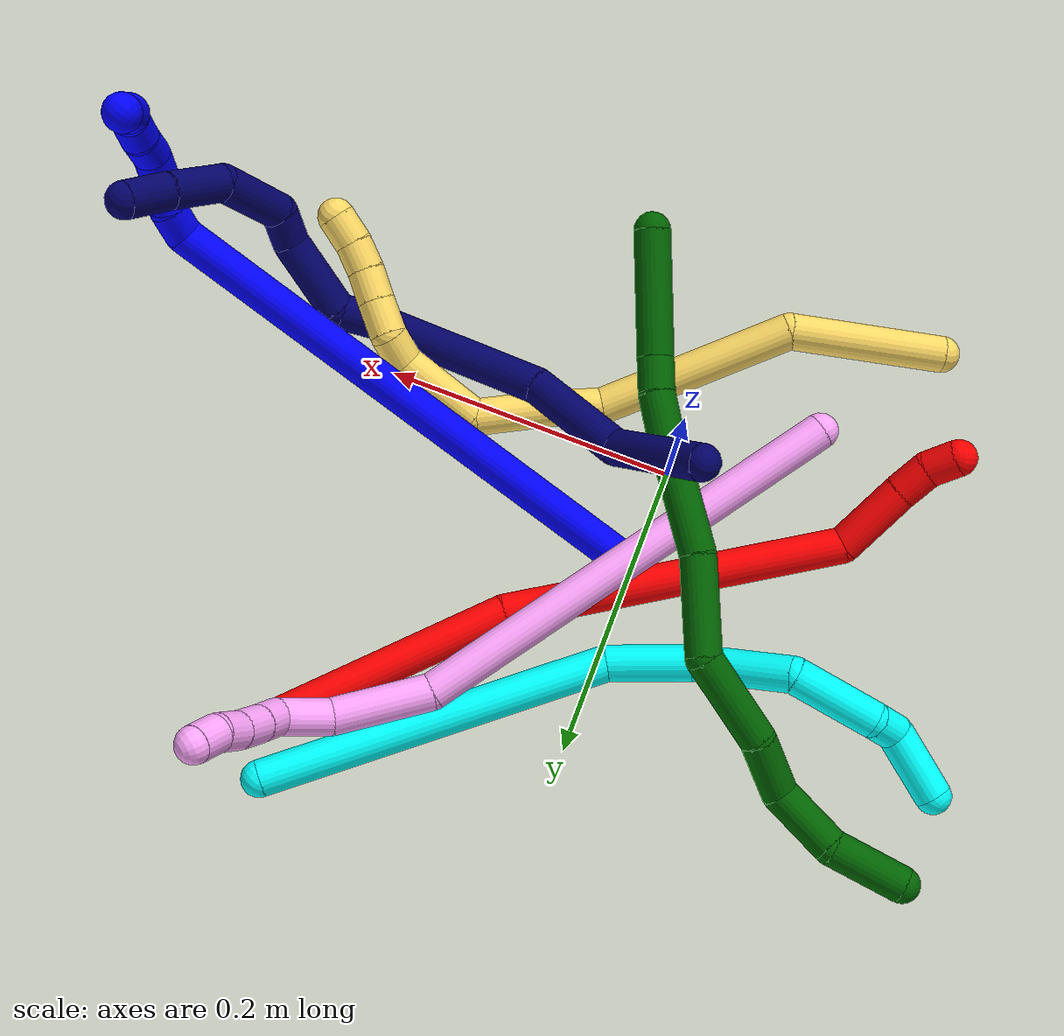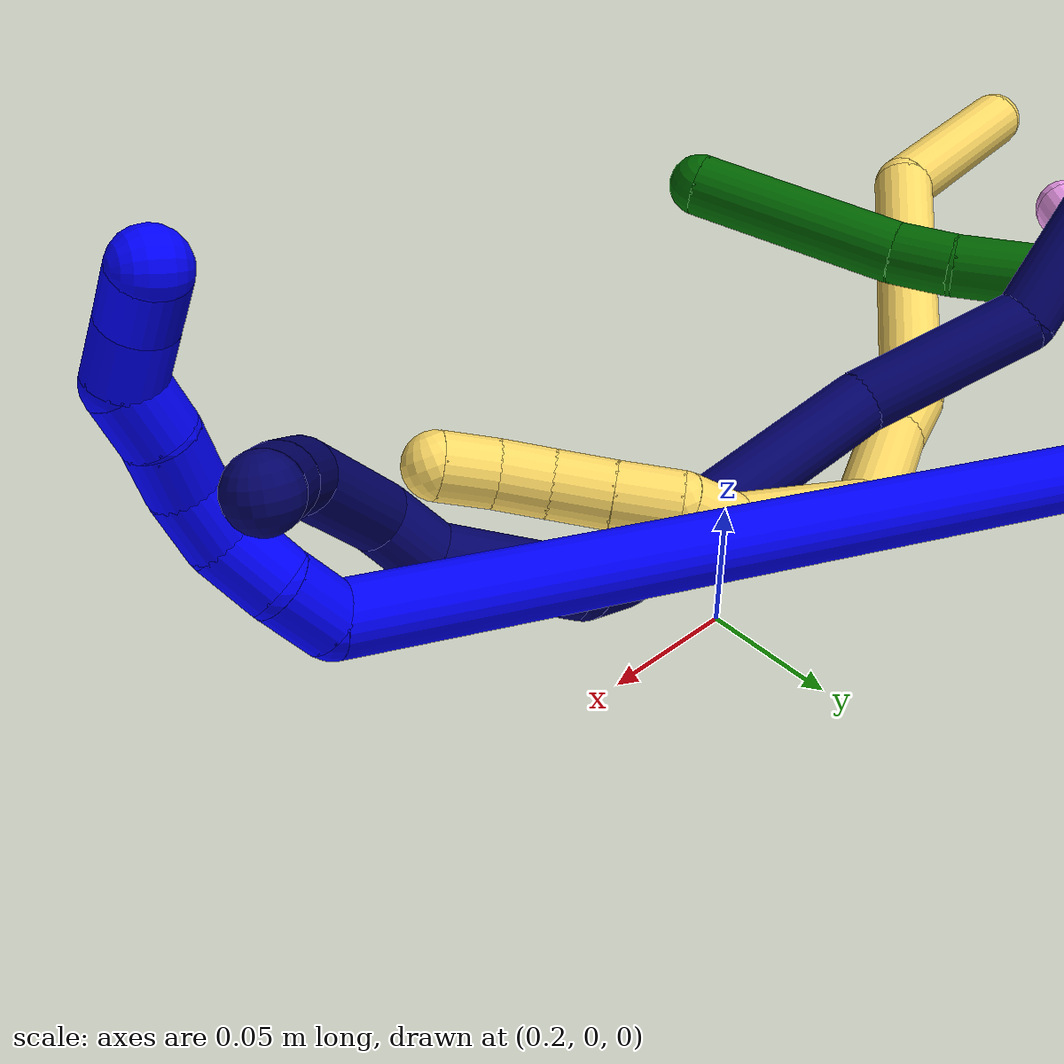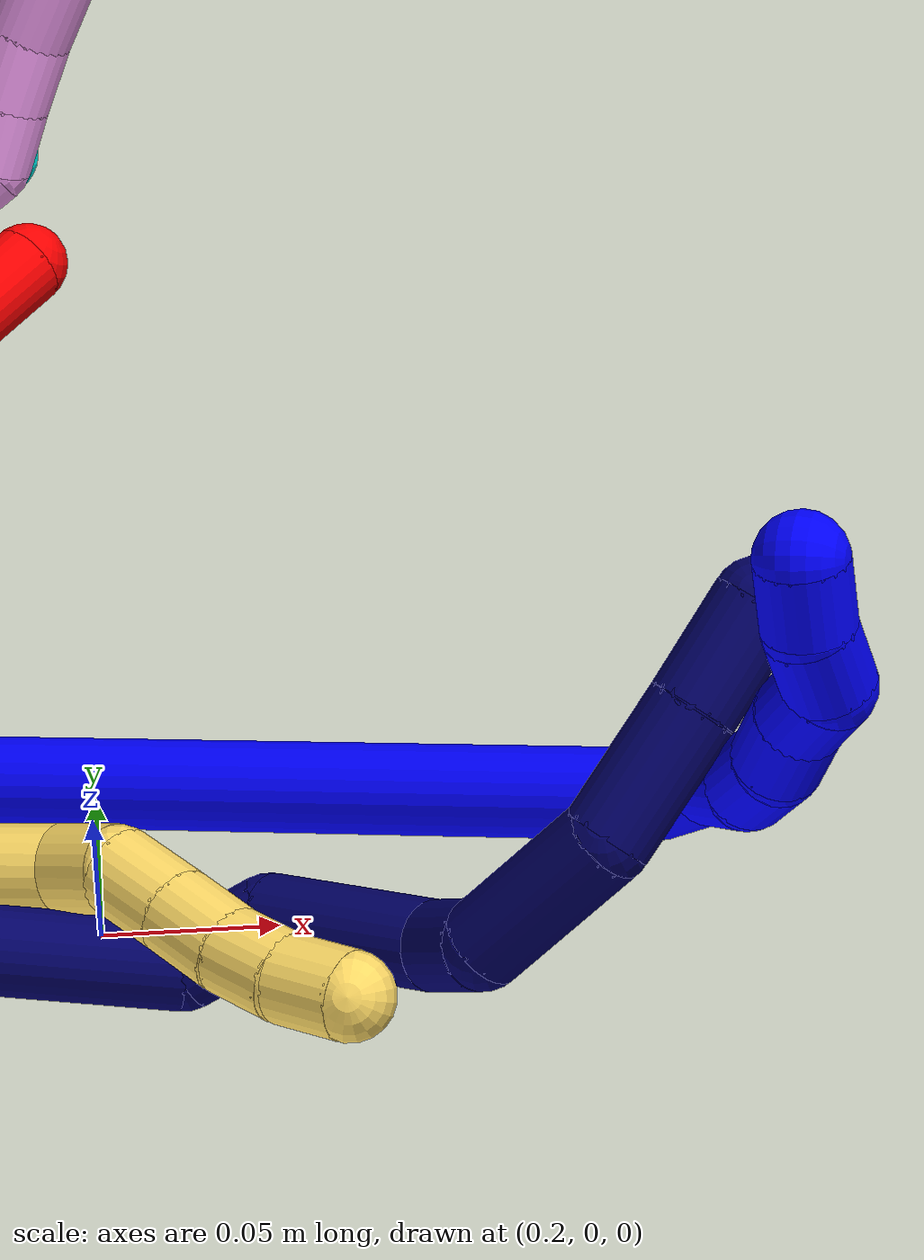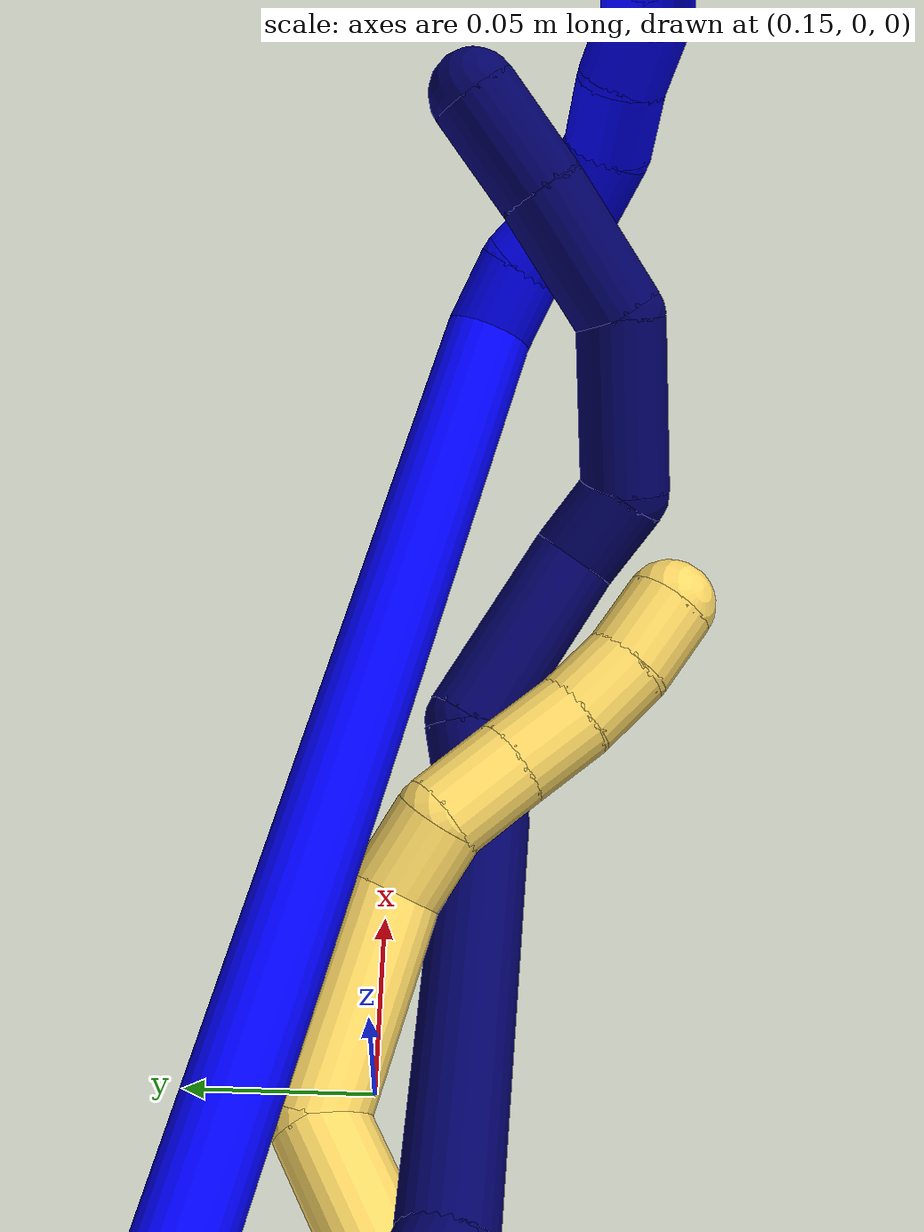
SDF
<sdf version="1.7">
 <world name="default">
  <plugin name="TubeGeneratorPlugin" filename="libtube_generator_plugin.so"/>
  <model name="photoneo_s_sensor">
   <static>1</static>
   <pose>0 0 2 1.57079 1.57079 3.14159</pose>
   <link name="link">
    <inertial><mass>0.1</mass></inertial>
    <sensor name="sensor" type="depth">
     <update_rate>30</update_rate>
     <camera>
      <horizontal_fov>1.22</horizontal_fov>
      <image><width>1920</width><height>1200</height><format>B8G8R8</format></image>
      <clip><near>0.1</near><far>4</far></clip>
      <depth_camera><output>points</output></depth_camera>
     </camera>
     <plugin name="camera_plugin" filename="libgazebo_ros_depth_camera.so">
      <baseline>0.2</baseline>
      <alwaysOn>1</alwaysOn>
      <updateRate>0.0</updateRate>
      <cameraName>camera_ir</cameraName>
      <imageTopicName>/camera/color/image_raw</imageTopicName>
      <cameraInfoTopicName>/camera/color/camera_info</cameraInfoTopicName>
      <depthImageTopicName>/camera/depth/image_raw</depthImageTopicName>
      <depthImageCameraInfoTopicName>/camera/depth/camera_info</depthImageCameraInfoTopicName>
      <pointCloudTopicName>/camera/depth/points</pointCloudTopicName>
      <frameName>fr_optical</frameName>
      <pointCloudCutoff>0.1</pointCloudCutoff>
      <pointCloudCutoffMax>2.0</pointCloudCutoffMax>
      <distortionK1>0</distortionK1>
      <distortionK2>0</distortionK2>
      <distortionK3>0</distortionK3>
      <distortionT1>0</distortionT1>
      <distortionT2>0</distortionT2>
      <CxPrime>0</CxPrime>
      <Cx>0</Cx>
      <Cy>0</Cy>
      <focalLength>0</focalLength>
      <hackBaseline>0</hackBaseline>
     </plugin>
    </sensor>
   </link>
  </model>
  <gravity>0 0 -9.8</gravity>
  <magnetic_field>6e-06 2.3e-05 -4.2e-05</magnetic_field>
  <atmosphere type="adiabatic"/>
  <physics name="default_physics" default="0" type="ode">
   <max_step_size>0.003</max_step_size>
   <real_time_factor>1</real_time_factor>
   <real_time_update_rate>1000</real_time_update_rate>
   <max_contacts>10000</max_contacts>
   <ode>
    <solver>
     <type>quick</type>
     <iters>100</iters>
     <sor>1.3</sor>
     <use_dynamic_moi_rescaling>0</use_dynamic_moi_rescaling>
    </solver>
    <constraints>
     <contact_max_correcting_vel>0</contact_max_correcting_vel>
     <contact_surface_layer>0.001</contact_surface_layer>
     <cfm>0</cfm>
     <erp>0.2</erp>
    </constraints>
   </ode>
  </physics>
  <scene><ambient>0.4 0.4 0.4 1</ambient><background>0.7 0.7 0.7 1</background><shadows>0</shadows></scene>
  <audio><device>default</device></audio>
  <spherical_coordinates>
   <surface_model>EARTH_WGS84</surface_model>
   <latitude_deg>0</latitude_deg>
   <longitude_deg>0</longitude_deg>
   <elevation>0</elevation>
   <heading_deg>0</heading_deg>
  </spherical_coordinates>
  <model name="bin">
   <static>1</static>
   <link name="bottom">
    <collision name="collision-bottom">
     <pose>0 0 -0.01 0 -0 0</pose>
     <geometry><box><size>0.8 0.6 0.02</size></box></geometry>
     <surface>
      <friction><ode><mu>100</mu><mu2>100</mu2></ode></friction>
      <contact><collide_bitmask>65535</collide_bitmask></contact>
     </surface>
    </collision>
   </link>
   <link name="west_wall">
    <collision name="collision-west_wall">
     <pose>-0.41 0 0.1 0 -0 0</pose>
     <geometry><box><size>0.02 0.6 0.2</size></box></geometry>
     <surface>
      <friction><ode><mu>100</mu><mu2>100</mu2></ode></friction>
      <contact><collide_bitmask>65535</collide_bitmask></contact>
     </surface>
    </collision>
   </link>
   <link name="east_wall">
    <collision name="collision-east_wall">
     <pose>0.41 0 0.1 0 -0 0</pose>
     <geometry><box><size>0.02 0.6 0.2</size></box></geometry>
     <surface>
      <friction><ode><mu>100</mu><mu2>100</mu2></ode></friction>
      <contact><collide_bitmask>65535</collide_bitmask></contact>
     </surface>
    </collision>
   </link>
   <link name="south_wall">
    <collision name="collision-south_wall">
     <pose>0 -0.31 0.1 0 -0 0</pose>
     <geometry><box><size>0.8 0.02 0.2</size></box></geometry>
     <surface>
      <friction><ode><mu>100</mu><mu2>100</mu2></ode></friction>
      <contact><collide_bitmask>65535</collide_bitmask></contact>
     </surface>
    </collision>
   </link>
   <link name="north_wall">
    <collision name="collision-north_wall">
     <pose>0 0.31 0.1 0 -0 0</pose>
     <geometry><box><size>0.8 0.02 0.2</size></box></geometry>
     <surface>
      <friction><ode><mu>100</mu><mu2>100</mu2></ode></friction>
      <contact><collide_bitmask>65535</collide_bitmask></contact>
     </surface>
    </collision>
   </link>
  </model>
  <model name="1">
   <static>0</static>
   <link name="1">
    <collision name="collision-cylinder-e_1_1_4">
     <pose>-0.001566 -0.007687 0.177678 0.043237 -0.008804 -0.00019</pose>
     <geometry><cylinder><radius>0.0125</radius><length>0.355702</length></cylinder></geometry>
     <surface>
      <friction><ode><mu>1.16</mu><mu2>1.16</mu2><slip1>0</slip1><slip2>0</slip2></ode></friction>
      <contact><ode><kp>1e+06</kp><kd>1</kd><max_vel>0</max_vel><min_depth>0.001</min_depth></ode></contact>
     </surface>
    </collision>
    <visual name="visual-cylinder-e_1_1_4">
     <pose>-0.001566 -0.007687 0.177678 0.043237 -0.008804 -0.00019</pose>
     <geometry><cylinder><radius>0.0125</radius><length>0.355702</length></cylinder></geometry>
     <material><ambient>0 0 1 1</ambient></material>
    </visual>
    <collision name="collision-cylinder-e_2_4_5">
     <pose>0.00257 -0.01144 0.363805 -0.435722 0.549009 -0.124523</pose>
     <geometry><cylinder><radius>0.0125</radius><length>0.021851</length></cylinder></geometry>
     <surface>
      <friction><ode><mu>1.16</mu><mu2>1.16</mu2><slip1>0</slip1><slip2>0</slip2></ode></friction>
      <contact><ode><kp>1e+06</kp><kd>1</kd><max_vel>0</max_vel><min_depth>0.001</min_depth></ode></contact>
     </surface>
    </collision>
    <visual name="visual-cylinder-e_2_4_5">
     <pose>0.00257 -0.01144 0.363805 -0.435722 0.549009 -0.124523</pose>
     <geometry><cylinder><radius>0.0125</radius><length>0.021851</length></cylinder></geometry>
     <material><ambient>0 0 1 1</ambient></material>
    </visual>
    <collision name="collision-cylinder-e_3_5_6">
     <pose>0.012336 -0.000748 0.379613 -0.742903 0.386412 -0.152128</pose>
     <geometry><cylinder><radius>0.0125</radius><length>0.021573</length></cylinder></geometry>
     <surface>
      <friction><ode><mu>1.16</mu><mu2>1.16</mu2><slip1>0</slip1><slip2>0</slip2></ode></friction>
      <contact><ode><kp>1e+06</kp><kd>1</kd><max_vel>0</max_vel><min_depth>0.001</min_depth></ode></contact>
     </surface>
    </collision>
    <visual name="visual-cylinder-e_3_5_6">
     <pose>0.012336 -0.000748 0.379613 -0.742903 0.386412 -0.152128</pose>
     <geometry><cylinder><radius>0.0125</radius><length>0.021573</length></cylinder></geometry>
     <material><ambient>0 0 1 1</ambient></material>
    </visual>
    <collision name="collision-cylinder-e_4_6_7">
     <pose>0.023668 0.010847 0.392634 -0.706877 0.773091 -0.298099</pose>
     <geometry><cylinder><radius>0.0125</radius><length>0.020809</length></cylinder></geometry>
     <surface>
      <friction><ode><mu>1.16</mu><mu2>1.16</mu2><slip1>0</slip1><slip2>0</slip2></ode></friction>
      <contact><ode><kp>1e+06</kp><kd>1</kd><max_vel>0</max_vel><min_depth>0.001</min_depth></ode></contact>
     </surface>
    </collision>
    <visual name="visual-cylinder-e_4_6_7">
     <pose>0.023668 0.010847 0.392634 -0.706877 0.773091 -0.298099</pose>
     <geometry><cylinder><radius>0.0125</radius><length>0.020809</length></cylinder></geometry>
     <material><ambient>0 0 1 1</ambient></material>
    </visual>
    <collision name="collision-cylinder-e_5_7_8">
     <pose>0.039541 0.018178 0.402748 -0.510825 1.03573 -0.295365</pose>
     <geometry><cylinder><radius>0.0125</radius><length>0.020013</length></cylinder></geometry>
     <surface>
      <friction><ode><mu>1.16</mu><mu2>1.16</mu2><slip1>0</slip1><slip2>0</slip2></ode></friction>
      <contact><ode><kp>1e+06</kp><kd>1</kd><max_vel>0</max_vel><min_depth>0.001</min_depth></ode></contact>
     </surface>
    </collision>
    <visual name="visual-cylinder-e_5_7_8">
     <pose>0.039541 0.018178 0.402748 -0.510825 1.03573 -0.295365</pose>
     <geometry><cylinder><radius>0.0125</radius><length>0.020013</length></cylinder></geometry>
     <material><ambient>0 0 1 1</ambient></material>
    </visual>
    <collision name="collision-cylinder-e_6_8_9">
     <pose>0.055709 0.0243 0.412673 -0.585214 0.855601 -0.273012</pose>
     <geometry><cylinder><radius>0.0125</radius><length>0.020028</length></cylinder></geometry>
     <surface>
      <friction><ode><mu>1.16</mu><mu2>1.16</mu2><slip1>0</slip1><slip2>0</slip2></ode></friction>
      <contact><ode><kp>1e+06</kp><kd>1</kd><max_vel>0</max_vel><min_depth>0.001</min_depth></ode></contact>
     </surface>
    </collision>
    <visual name="visual-cylinder-e_6_8_9">
     <pose>0.055709 0.0243 0.412673 -0.585214 0.855601 -0.273012</pose>
     <geometry><cylinder><radius>0.0125</radius><length>0.020028</length></cylinder></geometry>
     <material><ambient>0 0 1 1</ambient></material>
    </visual>
    <collision name="collision-cylinder-e_7_9_10">
     <pose>0.073004 0.029903 0.416972 -2.10718 1.33888 -1.89506</pose>
     <geometry><cylinder><radius>0.0125</radius><length>0.020004</length></cylinder></geometry>
     <surface>
      <friction><ode><mu>1.16</mu><mu2>1.16</mu2><slip1>0</slip1><slip2>0</slip2></ode></friction>
      <contact><ode><kp>1e+06</kp><kd>1</kd><max_vel>0</max_vel><min_depth>0.001</min_depth></ode></contact>
     </surface>
    </collision>
    <visual name="visual-cylinder-e_7_9_10">
     <pose>0.073004 0.029903 0.416972 -2.10718 1.33888 -1.89506</pose>
     <geometry><cylinder><radius>0.0125</radius><length>0.020004</length></cylinder></geometry>
     <material><ambient>0 0 1 1</ambient></material>
    </visual>
    <collision name="collision-cylinder-e_8_10_2">
     <pose>0.09274 0.031463 0.415761 1.65754 1.52901 1.61583</pose>
     <geometry><cylinder><radius>0.0125</radius><length>0.020019</length></cylinder></geometry>
     <surface>
      <friction><ode><mu>1.16</mu><mu2>1.16</mu2><slip1>0</slip1><slip2>0</slip2></ode></friction>
      <contact><ode><kp>1e+06</kp><kd>1</kd><max_vel>0</max_vel><min_depth>0.001</min_depth></ode></contact>
     </surface>
    </collision>
    <visual name="visual-cylinder-e_8_10_2">
     <pose>0.09274 0.031463 0.415761 1.65754 1.52901 1.61583</pose>
     <geometry><cylinder><radius>0.0125</radius><length>0.020019</length></cylinder></geometry>
     <material><ambient>0 0 1 1</ambient></material>
    </visual>
    <collision name="collision-sphere-2">
     <pose>0.102741 0.031046 0.415725 0 -0 0</pose>
     <geometry><sphere><radius>0.0125</radius></sphere></geometry>
     <surface>
      <friction><ode><mu>1.16</mu><mu2>1.16</mu2><slip1>0</slip1><slip2>0</slip2></ode></friction>
      <contact><ode><kp>1e+06</kp><kd>1</kd><max_vel>0</max_vel><min_depth>0.001</min_depth></ode></contact>
     </surface>
    </collision>
    <visual name="visual-sphere-2">
     <pose>0.102741 0.031046 0.415725 0 -0 0</pose>
     <geometry><sphere><radius>0.0125</radius></sphere></geometry>
     <material><ambient>0 0 1 1</ambient></material>
    </visual>
    <collision name="collision-sphere-10">
     <pose>0.082739 0.031879 0.415797 0 -0 0</pose>
     <geometry><sphere><radius>0.0125</radius></sphere></geometry>
     <surface>
      <friction><ode><mu>1.16</mu><mu2>1.16</mu2><slip1>0</slip1><slip2>0</slip2></ode></friction>
      <contact><ode><kp>1e+06</kp><kd>1</kd><max_vel>0</max_vel><min_depth>0.001</min_depth></ode></contact>
     </surface>
    </collision>
    <visual name="visual-sphere-10">
     <pose>0.082739 0.031879 0.415797 0 -0 0</pose>
     <geometry><sphere><radius>0.0125</radius></sphere></geometry>
     <material><ambient>0 0 1 1</ambient></material>
    </visual>
    <collision name="collision-sphere-9">
     <pose>0.06327 0.027927 0.418147 0 -0 0</pose>
     <geometry><sphere><radius>0.0125</radius></sphere></geometry>
     <surface>
      <friction><ode><mu>1.16</mu><mu2>1.16</mu2><slip1>0</slip1><slip2>0</slip2></ode></friction>
      <contact><ode><kp>1e+06</kp><kd>1</kd><max_vel>0</max_vel><min_depth>0.001</min_depth></ode></contact>
     </surface>
    </collision>
    <visual name="visual-sphere-9">
     <pose>0.06327 0.027927 0.418147 0 -0 0</pose>
     <geometry><sphere><radius>0.0125</radius></sphere></geometry>
     <material><ambient>0 0 1 1</ambient></material>
    </visual>
    <collision name="collision-sphere-4">
     <pose>-0.003131 -0.015374 0.355356 0 -0 0</pose>
     <geometry><sphere><radius>0.0125</radius></sphere></geometry>
     <surface>
      <friction><ode><mu>1.16</mu><mu2>1.16</mu2><slip1>0</slip1><slip2>0</slip2></ode></friction>
      <contact><ode><kp>1e+06</kp><kd>1</kd><max_vel>0</max_vel><min_depth>0.001</min_depth></ode></contact>
     </surface>
    </collision>
    <visual name="visual-sphere-4">
     <pose>-0.003131 -0.015374 0.355356 0 -0 0</pose>
     <geometry><sphere><radius>0.0125</radius></sphere></geometry>
     <material><ambient>0 0 1 1</ambient></material>
    </visual>
    <collision name="collision-sphere-1">
     <geometry><sphere><radius>0.0125</radius></sphere></geometry>
     <surface>
      <friction><ode><mu>1.16</mu><mu2>1.16</mu2><slip1>0</slip1><slip2>0</slip2></ode></friction>
      <contact><ode><kp>1e+06</kp><kd>1</kd><max_vel>0</max_vel><min_depth>0.001</min_depth></ode></contact>
     </surface>
    </collision>
    <visual name="visual-sphere-1">
     <geometry><sphere><radius>0.0125</radius></sphere></geometry>
     <material><ambient>0 0 1 1</ambient></material>
    </visual>
    <collision name="collision-sphere-8">
     <pose>0.048149 0.020672 0.407198 0 -0 0</pose>
     <geometry><sphere><radius>0.0125</radius></sphere></geometry>
     <surface>
      <friction><ode><mu>1.16</mu><mu2>1.16</mu2><slip1>0</slip1><slip2>0</slip2></ode></friction>
      <contact><ode><kp>1e+06</kp><kd>1</kd><max_vel>0</max_vel><min_depth>0.001</min_depth></ode></contact>
     </surface>
    </collision>
    <visual name="visual-sphere-8">
     <pose>0.048149 0.020672 0.407198 0 -0 0</pose>
     <geometry><sphere><radius>0.0125</radius></sphere></geometry>
     <material><ambient>0 0 1 1</ambient></material>
    </visual>
    <collision name="collision-sphere-5">
     <pose>0.008271 -0.007507 0.372254 0 -0 0</pose>
     <geometry><sphere><radius>0.0125</radius></sphere></geometry>
     <surface>
      <friction><ode><mu>1.16</mu><mu2>1.16</mu2><slip1>0</slip1><slip2>0</slip2></ode></friction>
      <contact><ode><kp>1e+06</kp><kd>1</kd><max_vel>0</max_vel><min_depth>0.001</min_depth></ode></contact>
     </surface>
    </collision>
    <visual name="visual-sphere-5">
     <pose>0.008271 -0.007507 0.372254 0 -0 0</pose>
     <geometry><sphere><radius>0.0125</radius></sphere></geometry>
     <material><ambient>0 0 1 1</ambient></material>
    </visual>
    <collision name="collision-sphere-6">
     <pose>0.016402 0.00601 0.386971 0 -0 0</pose>
     <geometry><sphere><radius>0.0125</radius></sphere></geometry>
     <surface>
      <friction><ode><mu>1.16</mu><mu2>1.16</mu2><slip1>0</slip1><slip2>0</slip2></ode></friction>
      <contact><ode><kp>1e+06</kp><kd>1</kd><max_vel>0</max_vel><min_depth>0.001</min_depth></ode></contact>
     </surface>
    </collision>
    <visual name="visual-sphere-6">
     <pose>0.016402 0.00601 0.386971 0 -0 0</pose>
     <geometry><sphere><radius>0.0125</radius></sphere></geometry>
     <material><ambient>0 0 1 1</ambient></material>
    </visual>
    <collision name="collision-sphere-7">
     <pose>0.030934 0.015683 0.398297 0 -0 0</pose>
     <geometry><sphere><radius>0.0125</radius></sphere></geometry>
     <surface>
      <friction><ode><mu>1.16</mu><mu2>1.16</mu2><slip1>0</slip1><slip2>0</slip2></ode></friction>
      <contact><ode><kp>1e+06</kp><kd>1</kd><max_vel>0</max_vel><min_depth>0.001</min_depth></ode></contact>
     </surface>
    </collision>
    <visual name="visual-sphere-7">
     <pose>0.030934 0.015683 0.398297 0 -0 0</pose>
     <geometry><sphere><radius>0.0125</radius></sphere></geometry>
     <material><ambient>0 0 1 1</ambient></material>
    </visual>
    <inertial>
     <pose>0.010964 -0.001392 0.240999 0 -0 0</pose>
     <mass>0.5</mass>
     <inertia>
      <ixx>0.003776</ixx>
      <ixy>0</ixy>
      <ixz>0</ixz>
      <iyy>0.003771</iyy>
      <iyz>0</iyz>
      <izz>0.000217</izz>
     </inertia>
    </inertial>
   </link>
   <pose>0.013234 0.064981 0.011856 0.830226 -1.27227 1.98934</pose>
  </model>
  <model name="2">
   <static>0</static>
   <link name="2">
    <collision name="collision-cylinder-e_1_1_4">
     <pose>-0.030036 -0.052228 -0.058912 2.41626 -0.364463 -0.904189</pose>
     <geometry><cylinder><radius>0.0125</radius><length>0.168531</length></cylinder></geometry>
     <surface>
      <friction><ode><mu>1.16</mu><mu2>1.16</mu2><slip1>0</slip1><slip2>0</slip2></ode></friction>
      <contact><ode><kp>1e+06</kp><kd>1</kd><max_vel>0</max_vel><min_depth>0.001</min_depth></ode></contact>
     </surface>
    </collision>
    <visual name="visual-cylinder-e_1_1_4">
     <pose>-0.030036 -0.052228 -0.058912 2.41626 -0.364463 -0.904189</pose>
     <geometry><cylinder><radius>0.0125</radius><length>0.168531</length></cylinder></geometry>
     <material><ambient>1 0 0 1</ambient></material>
    </visual>
    <collision name="collision-cylinder-e_2_4_5">
     <pose>-0.124898 -0.159164 -0.197714 2.54115 -0.589967 -1.55211</pose>
     <geometry><cylinder><radius>0.0125</radius><length>0.233045</length></cylinder></geometry>
     <surface>
      <friction><ode><mu>1.16</mu><mu2>1.16</mu2><slip1>0</slip1><slip2>0</slip2></ode></friction>
      <contact><ode><kp>1e+06</kp><kd>1</kd><max_vel>0</max_vel><min_depth>0.001</min_depth></ode></contact>
     </surface>
    </collision>
    <visual name="visual-cylinder-e_2_4_5">
     <pose>-0.124898 -0.159164 -0.197714 2.54115 -0.589967 -1.55211</pose>
     <geometry><cylinder><radius>0.0125</radius><length>0.233045</length></cylinder></geometry>
     <material><ambient>1 0 0 1</ambient></material>
    </visual>
    <collision name="collision-cylinder-e_3_5_6">
     <pose>-0.198238 -0.23721 -0.286027 1.91722 -0.33058 -0.466479</pose>
     <geometry><cylinder><radius>0.0125</radius><length>0.052466</length></cylinder></geometry>
     <surface>
      <friction><ode><mu>1.16</mu><mu2>1.16</mu2><slip1>0</slip1><slip2>0</slip2></ode></friction>
      <contact><ode><kp>1e+06</kp><kd>1</kd><max_vel>0</max_vel><min_depth>0.001</min_depth></ode></contact>
     </surface>
    </collision>
    <visual name="visual-cylinder-e_3_5_6">
     <pose>-0.198238 -0.23721 -0.286027 1.91722 -0.33058 -0.466479</pose>
     <geometry><cylinder><radius>0.0125</radius><length>0.052466</length></cylinder></geometry>
     <material><ambient>1 0 0 1</ambient></material>
    </visual>
    <collision name="collision-cylinder-e_4_6_7">
     <pose>-0.211676 -0.27094 -0.297744 1.87762 -0.424203 -0.572098</pose>
     <geometry><cylinder><radius>0.0125</radius><length>0.023923</length></cylinder></geometry>
     <surface>
      <friction><ode><mu>1.16</mu><mu2>1.16</mu2><slip1>0</slip1><slip2>0</slip2></ode></friction>
      <contact><ode><kp>1e+06</kp><kd>1</kd><max_vel>0</max_vel><min_depth>0.001</min_depth></ode></contact>
     </surface>
    </collision>
    <visual name="visual-cylinder-e_4_6_7">
     <pose>-0.211676 -0.27094 -0.297744 1.87762 -0.424203 -0.572098</pose>
     <geometry><cylinder><radius>0.0125</radius><length>0.023923</length></cylinder></geometry>
     <material><ambient>1 0 0 1</ambient></material>
    </visual>
    <collision name="collision-cylinder-e_5_7_2">
     <pose>-0.224195 -0.288681 -0.304151 1.9717 -0.760682 -1.08628</pose>
     <geometry><cylinder><radius>0.0125</radius><length>0.022037</length></cylinder></geometry>
     <surface>
      <friction><ode><mu>1.16</mu><mu2>1.16</mu2><slip1>0</slip1><slip2>0</slip2></ode></friction>
      <contact><ode><kp>1e+06</kp><kd>1</kd><max_vel>0</max_vel><min_depth>0.001</min_depth></ode></contact>
     </surface>
    </collision>
    <visual name="visual-cylinder-e_5_7_2">
     <pose>-0.224195 -0.288681 -0.304151 1.9717 -0.760682 -1.08628</pose>
     <geometry><cylinder><radius>0.0125</radius><length>0.022037</length></cylinder></geometry>
     <material><ambient>1 0 0 1</ambient></material>
    </visual>
    <collision name="collision-sphere-2">
     <pose>-0.231792 -0.296029 -0.307266 0 -0 0</pose>
     <geometry><sphere><radius>0.0125</radius></sphere></geometry>
     <surface>
      <friction><ode><mu>1.16</mu><mu2>1.16</mu2><slip1>0</slip1><slip2>0</slip2></ode></friction>
      <contact><ode><kp>1e+06</kp><kd>1</kd><max_vel>0</max_vel><min_depth>0.001</min_depth></ode></contact>
     </surface>
    </collision>
    <visual name="visual-sphere-2">
     <pose>-0.231792 -0.296029 -0.307266 0 -0 0</pose>
     <geometry><sphere><radius>0.0125</radius></sphere></geometry>
     <material><ambient>1 0 0 1</ambient></material>
    </visual>
    <collision name="collision-sphere-7">
     <pose>-0.216599 -0.281332 -0.301037 0 -0 0</pose>
     <geometry><sphere><radius>0.0125</radius></sphere></geometry>
     <surface>
      <friction><ode><mu>1.16</mu><mu2>1.16</mu2><slip1>0</slip1><slip2>0</slip2></ode></friction>
      <contact><ode><kp>1e+06</kp><kd>1</kd><max_vel>0</max_vel><min_depth>0.001</min_depth></ode></contact>
     </surface>
    </collision>
    <visual name="visual-sphere-7">
     <pose>-0.216599 -0.281332 -0.301037 0 -0 0</pose>
     <geometry><sphere><radius>0.0125</radius></sphere></geometry>
     <material><ambient>1 0 0 1</ambient></material>
    </visual>
    <collision name="collision-sphere-6">
     <pose>-0.206753 -0.260548 -0.294452 0 -0 0</pose>
     <geometry><sphere><radius>0.0125</radius></sphere></geometry>
     <surface>
      <friction><ode><mu>1.16</mu><mu2>1.16</mu2><slip1>0</slip1><slip2>0</slip2></ode></friction>
      <contact><ode><kp>1e+06</kp><kd>1</kd><max_vel>0</max_vel><min_depth>0.001</min_depth></ode></contact>
     </surface>
    </collision>
    <visual name="visual-sphere-6">
     <pose>-0.206753 -0.260548 -0.294452 0 -0 0</pose>
     <geometry><sphere><radius>0.0125</radius></sphere></geometry>
     <material><ambient>1 0 0 1</ambient></material>
    </visual>
    <collision name="collision-sphere-5">
     <pose>-0.189723 -0.213871 -0.277603 0 -0 0</pose>
     <geometry><sphere><radius>0.0125</radius></sphere></geometry>
     <surface>
      <friction><ode><mu>1.16</mu><mu2>1.16</mu2><slip1>0</slip1><slip2>0</slip2></ode></friction>
      <contact><ode><kp>1e+06</kp><kd>1</kd><max_vel>0</max_vel><min_depth>0.001</min_depth></ode></contact>
     </surface>
    </collision>
    <visual name="visual-sphere-5">
     <pose>-0.189723 -0.213871 -0.277603 0 -0 0</pose>
     <geometry><sphere><radius>0.0125</radius></sphere></geometry>
     <material><ambient>1 0 0 1</ambient></material>
    </visual>
    <collision name="collision-sphere-1">
     <geometry><sphere><radius>0.0125</radius></sphere></geometry>
     <surface>
      <friction><ode><mu>1.16</mu><mu2>1.16</mu2><slip1>0</slip1><slip2>0</slip2></ode></friction>
      <contact><ode><kp>1e+06</kp><kd>1</kd><max_vel>0</max_vel><min_depth>0.001</min_depth></ode></contact>
     </surface>
    </collision>
    <visual name="visual-sphere-1">
     <geometry><sphere><radius>0.0125</radius></sphere></geometry>
     <material><ambient>1 0 0 1</ambient></material>
    </visual>
    <collision name="collision-sphere-4">
     <pose>-0.060072 -0.104457 -0.117825 0 -0 0</pose>
     <geometry><sphere><radius>0.0125</radius></sphere></geometry>
     <surface>
      <friction><ode><mu>1.16</mu><mu2>1.16</mu2><slip1>0</slip1><slip2>0</slip2></ode></friction>
      <contact><ode><kp>1e+06</kp><kd>1</kd><max_vel>0</max_vel><min_depth>0.001</min_depth></ode></contact>
     </surface>
    </collision>
    <visual name="visual-sphere-4">
     <pose>-0.060072 -0.104457 -0.117825 0 -0 0</pose>
     <geometry><sphere><radius>0.0125</radius></sphere></geometry>
     <material><ambient>1 0 0 1</ambient></material>
    </visual>
    <inertial>
     <pose>-0.109148 -0.142366 -0.169673 0 -0 0</pose>
     <mass>0.5</mass>
     <inertia>
      <ixx>-0.000943</ixx>
      <ixy>0</ixy>
      <ixz>0</ixz>
      <iyy>-0.001009</iyy>
      <iyz>0</iyz>
      <izz>0.001485</izz>
     </inertia>
    </inertial>
   </link>
   <pose>0.186507 0.24909 0.022735 -0.482882 0.611522 -0.265885</pose>
  </model>
  <model name="3">
   <static>0</static>
   <link name="3">
    <collision name="collision-cylinder-e_1_1_4">
     <pose>-0.111582 -0.017149 0.041565 0.391317 -1.18774 -0.26605</pose>
     <geometry><cylinder><radius>0.0125</radius><length>0.240602</length></cylinder></geometry>
     <surface>
      <friction><ode><mu>1.16</mu><mu2>1.16</mu2><slip1>0</slip1><slip2>0</slip2></ode></friction>
      <contact><ode><kp>1e+06</kp><kd>1</kd><max_vel>0</max_vel><min_depth>0.001</min_depth></ode></contact>
     </surface>
    </collision>
    <visual name="visual-cylinder-e_1_1_4">
     <pose>-0.111582 -0.017149 0.041565 0.391317 -1.18774 -0.26605</pose>
     <geometry><cylinder><radius>0.0125</radius><length>0.240602</length></cylinder></geometry>
     <material><ambient>0.003922 1 0.996078 1</ambient></material>
    </visual>
    <collision name="collision-cylinder-e_2_4_5">
     <pose>-0.245058 -0.03839 0.102449 0.208671 -0.836893 -0.093069</pose>
     <geometry><cylinder><radius>0.0125</radius><length>0.058968</length></cylinder></geometry>
     <surface>
      <friction><ode><mu>1.16</mu><mu2>1.16</mu2><slip1>0</slip1><slip2>0</slip2></ode></friction>
      <contact><ode><kp>1e+06</kp><kd>1</kd><max_vel>0</max_vel><min_depth>0.001</min_depth></ode></contact>
     </surface>
    </collision>
    <visual name="visual-cylinder-e_2_4_5">
     <pose>-0.245058 -0.03839 0.102449 0.208671 -0.836893 -0.093069</pose>
     <geometry><cylinder><radius>0.0125</radius><length>0.058968</length></cylinder></geometry>
     <material><ambient>0.003922 1 0.996078 1</ambient></material>
    </visual>
    <collision name="collision-cylinder-e_3_5_6">
     <pose>-0.284615 -0.053197 0.149144 0.373113 -0.540998 -0.104584</pose>
     <geometry><cylinder><radius>0.0125</radius><length>0.068594</length></cylinder></geometry>
     <surface>
      <friction><ode><mu>1.16</mu><mu2>1.16</mu2><slip1>0</slip1><slip2>0</slip2></ode></friction>
      <contact><ode><kp>1e+06</kp><kd>1</kd><max_vel>0</max_vel><min_depth>0.001</min_depth></ode></contact>
     </surface>
    </collision>
    <visual name="visual-cylinder-e_3_5_6">
     <pose>-0.284615 -0.053197 0.149144 0.373113 -0.540998 -0.104584</pose>
     <geometry><cylinder><radius>0.0125</radius><length>0.068594</length></cylinder></geometry>
     <material><ambient>0.003922 1 0.996078 1</ambient></material>
    </visual>
    <collision name="collision-cylinder-e_4_6_7">
     <pose>-0.316675 -0.05481 0.202013 -0.34302 -0.48881 0.086341</pose>
     <geometry><cylinder><radius>0.0125</radius><length>0.061318</length></cylinder></geometry>
     <surface>
      <friction><ode><mu>1.16</mu><mu2>1.16</mu2><slip1>0</slip1><slip2>0</slip2></ode></friction>
      <contact><ode><kp>1e+06</kp><kd>1</kd><max_vel>0</max_vel><min_depth>0.001</min_depth></ode></contact>
     </surface>
    </collision>
    <visual name="visual-cylinder-e_4_6_7">
     <pose>-0.316675 -0.05481 0.202013 -0.34302 -0.48881 0.086341</pose>
     <geometry><cylinder><radius>0.0125</radius><length>0.061318</length></cylinder></geometry>
     <material><ambient>0.003922 1 0.996078 1</ambient></material>
    </visual>
    <collision name="collision-cylinder-e_5_7_8">
     <pose>-0.33732 -0.038814 0.233177 -0.882114 -0.610803 0.295486</pose>
     <geometry><cylinder><radius>0.0125</radius><length>0.021792</length></cylinder></geometry>
     <surface>
      <friction><ode><mu>1.16</mu><mu2>1.16</mu2><slip1>0</slip1><slip2>0</slip2></ode></friction>
      <contact><ode><kp>1e+06</kp><kd>1</kd><max_vel>0</max_vel><min_depth>0.001</min_depth></ode></contact>
     </surface>
    </collision>
    <visual name="visual-cylinder-e_5_7_8">
     <pose>-0.33732 -0.038814 0.233177 -0.882114 -0.610803 0.295486</pose>
     <geometry><cylinder><radius>0.0125</radius><length>0.021792</length></cylinder></geometry>
     <material><ambient>0.003922 1 0.996078 1</ambient></material>
    </visual>
    <collision name="collision-cylinder-e_6_8_2">
     <pose>-0.34322 -0.020548 0.260391 -0.485829 0.014353 -0.003557</pose>
     <geometry><cylinder><radius>0.0125</radius><length>0.048726</length></cylinder></geometry>
     <surface>
      <friction><ode><mu>1.16</mu><mu2>1.16</mu2><slip1>0</slip1><slip2>0</slip2></ode></friction>
      <contact><ode><kp>1e+06</kp><kd>1</kd><max_vel>0</max_vel><min_depth>0.001</min_depth></ode></contact>
     </surface>
    </collision>
    <visual name="visual-cylinder-e_6_8_2">
     <pose>-0.34322 -0.020548 0.260391 -0.485829 0.014353 -0.003557</pose>
     <geometry><cylinder><radius>0.0125</radius><length>0.048726</length></cylinder></geometry>
     <material><ambient>0.003922 1 0.996078 1</ambient></material>
    </visual>
    <collision name="collision-sphere-2">
     <pose>-0.34287 -0.009173 0.281933 0 -0 0</pose>
     <geometry><sphere><radius>0.0125</radius></sphere></geometry>
     <surface>
      <friction><ode><mu>1.16</mu><mu2>1.16</mu2><slip1>0</slip1><slip2>0</slip2></ode></friction>
      <contact><ode><kp>1e+06</kp><kd>1</kd><max_vel>0</max_vel><min_depth>0.001</min_depth></ode></contact>
     </surface>
    </collision>
    <visual name="visual-sphere-2">
     <pose>-0.34287 -0.009173 0.281933 0 -0 0</pose>
     <geometry><sphere><radius>0.0125</radius></sphere></geometry>
     <material><ambient>0.003922 1 0.996078 1</ambient></material>
    </visual>
    <collision name="collision-sphere-4">
     <pose>-0.223164 -0.034299 0.083129 0 -0 0</pose>
     <geometry><sphere><radius>0.0125</radius></sphere></geometry>
     <surface>
      <friction><ode><mu>1.16</mu><mu2>1.16</mu2><slip1>0</slip1><slip2>0</slip2></ode></friction>
      <contact><ode><kp>1e+06</kp><kd>1</kd><max_vel>0</max_vel><min_depth>0.001</min_depth></ode></contact>
     </surface>
    </collision>
    <visual name="visual-sphere-4">
     <pose>-0.223164 -0.034299 0.083129 0 -0 0</pose>
     <geometry><sphere><radius>0.0125</radius></sphere></geometry>
     <material><ambient>0.003922 1 0.996078 1</ambient></material>
    </visual>
    <collision name="collision-sphere-1">
     <geometry><sphere><radius>0.0125</radius></sphere></geometry>
     <surface>
      <friction><ode><mu>1.16</mu><mu2>1.16</mu2><slip1>0</slip1><slip2>0</slip2></ode></friction>
      <contact><ode><kp>1e+06</kp><kd>1</kd><max_vel>0</max_vel><min_depth>0.001</min_depth></ode></contact>
     </surface>
    </collision>
    <visual name="visual-sphere-1">
     <geometry><sphere><radius>0.0125</radius></sphere></geometry>
     <material><ambient>0.003922 1 0.996078 1</ambient></material>
    </visual>
    <collision name="collision-sphere-8">
     <pose>-0.343569 -0.031923 0.23885 0 -0 0</pose>
     <geometry><sphere><radius>0.0125</radius></sphere></geometry>
     <surface>
      <friction><ode><mu>1.16</mu><mu2>1.16</mu2><slip1>0</slip1><slip2>0</slip2></ode></friction>
      <contact><ode><kp>1e+06</kp><kd>1</kd><max_vel>0</max_vel><min_depth>0.001</min_depth></ode></contact>
     </surface>
    </collision>
    <visual name="visual-sphere-8">
     <pose>-0.343569 -0.031923 0.23885 0 -0 0</pose>
     <geometry><sphere><radius>0.0125</radius></sphere></geometry>
     <material><ambient>0.003922 1 0.996078 1</ambient></material>
    </visual>
    <collision name="collision-sphere-5">
     <pose>-0.266952 -0.042481 0.121768 0 -0 0</pose>
     <geometry><sphere><radius>0.0125</radius></sphere></geometry>
     <surface>
      <friction><ode><mu>1.16</mu><mu2>1.16</mu2><slip1>0</slip1><slip2>0</slip2></ode></friction>
      <contact><ode><kp>1e+06</kp><kd>1</kd><max_vel>0</max_vel><min_depth>0.001</min_depth></ode></contact>
     </surface>
    </collision>
    <visual name="visual-sphere-5">
     <pose>-0.266952 -0.042481 0.121768 0 -0 0</pose>
     <geometry><sphere><radius>0.0125</radius></sphere></geometry>
     <material><ambient>0.003922 1 0.996078 1</ambient></material>
    </visual>
    <collision name="collision-sphere-6">
     <pose>-0.302278 -0.063914 0.176521 0 -0 0</pose>
     <geometry><sphere><radius>0.0125</radius></sphere></geometry>
     <surface>
      <friction><ode><mu>1.16</mu><mu2>1.16</mu2><slip1>0</slip1><slip2>0</slip2></ode></friction>
      <contact><ode><kp>1e+06</kp><kd>1</kd><max_vel>0</max_vel><min_depth>0.001</min_depth></ode></contact>
     </surface>
    </collision>
    <visual name="visual-sphere-6">
     <pose>-0.302278 -0.063914 0.176521 0 -0 0</pose>
     <geometry><sphere><radius>0.0125</radius></sphere></geometry>
     <material><ambient>0.003922 1 0.996078 1</ambient></material>
    </visual>
    <collision name="collision-sphere-7">
     <pose>-0.331071 -0.045705 0.227505 0 -0 0</pose>
     <geometry><sphere><radius>0.0125</radius></sphere></geometry>
     <surface>
      <friction><ode><mu>1.16</mu><mu2>1.16</mu2><slip1>0</slip1><slip2>0</slip2></ode></friction>
      <contact><ode><kp>1e+06</kp><kd>1</kd><max_vel>0</max_vel><min_depth>0.001</min_depth></ode></contact>
     </surface>
    </collision>
    <visual name="visual-sphere-7">
     <pose>-0.331071 -0.045705 0.227505 0 -0 0</pose>
     <geometry><sphere><radius>0.0125</radius></sphere></geometry>
     <material><ambient>0.003922 1 0.996078 1</ambient></material>
    </visual>
    <inertial>
     <pose>-0.208626 -0.030494 0.112857 0 -0 0</pose>
     <mass>0.5</mass>
     <inertia>
      <ixx>0.000348</ixx>
      <ixy>0</ixy>
      <ixz>0</ixz>
      <iyy>0.001114</iyy>
      <iyz>0</iyz>
      <izz>0.001314</izz>
     </inertia>
    </inertial>
   </link>
   <pose>0.178856 0.288255 0.032273 -1.21595 -0.356933 0.966239</pose>
  </model>
  <model name="4">
   <static>0</static>
   <link name="4">
    <collision name="collision-cylinder-e_1_1_4">
     <pose>0.019927 0.047858 0.147684 -0.313379 0.127658 -0.020195</pose>
     <geometry><cylinder><radius>0.0125</radius><length>0.313037</length></cylinder></geometry>
     <surface>
      <friction><ode><mu>1.16</mu><mu2>1.16</mu2><slip1>0</slip1><slip2>0</slip2></ode></friction>
      <contact><ode><kp>1e+06</kp><kd>1</kd><max_vel>0</max_vel><min_depth>0.001</min_depth></ode></contact>
     </surface>
    </collision>
    <visual name="visual-cylinder-e_1_1_4">
     <pose>0.019927 0.047858 0.147684 -0.313379 0.127658 -0.020195</pose>
     <geometry><cylinder><radius>0.0125</radius><length>0.313037</length></cylinder></geometry>
     <material><ambient>1 0.65098 0.996078 1</ambient></material>
    </visual>
    <collision name="collision-cylinder-e_2_4_5">
     <pose>0.051668 0.096929 0.326991 -0.038335 0.357299 -0.006923</pose>
     <geometry><cylinder><radius>0.0125</radius><length>0.06756</length></cylinder></geometry>
     <surface>
      <friction><ode><mu>1.16</mu><mu2>1.16</mu2><slip1>0</slip1><slip2>0</slip2></ode></friction>
      <contact><ode><kp>1e+06</kp><kd>1</kd><max_vel>0</max_vel><min_depth>0.001</min_depth></ode></contact>
     </surface>
    </collision>
    <visual name="visual-cylinder-e_2_4_5">
     <pose>0.051668 0.096929 0.326991 -0.038335 0.357299 -0.006923</pose>
     <geometry><cylinder><radius>0.0125</radius><length>0.06756</length></cylinder></geometry>
     <material><ambient>1 0.65098 0.996078 1</ambient></material>
    </visual>
    <collision name="collision-cylinder-e_3_5_6">
     <pose>0.067777 0.090882 0.375006 0.416909 0.235115 0.049953</pose>
     <geometry><cylinder><radius>0.0125</radius><length>0.036869</length></cylinder></geometry>
     <surface>
      <friction><ode><mu>1.16</mu><mu2>1.16</mu2><slip1>0</slip1><slip2>0</slip2></ode></friction>
      <contact><ode><kp>1e+06</kp><kd>1</kd><max_vel>0</max_vel><min_depth>0.001</min_depth></ode></contact>
     </surface>
    </collision>
    <visual name="visual-cylinder-e_3_5_6">
     <pose>0.067777 0.090882 0.375006 0.416909 0.235115 0.049953</pose>
     <geometry><cylinder><radius>0.0125</radius><length>0.036869</length></cylinder></geometry>
     <material><ambient>1 0.65098 0.996078 1</ambient></material>
    </visual>
    <collision name="collision-cylinder-e_4_6_7">
     <pose>0.068544 0.07868 0.399373 0.554907 -0.359551 -0.103425</pose>
     <geometry><cylinder><radius>0.0125</radius><length>0.020047</length></cylinder></geometry>
     <surface>
      <friction><ode><mu>1.16</mu><mu2>1.16</mu2><slip1>0</slip1><slip2>0</slip2></ode></friction>
      <contact><ode><kp>1e+06</kp><kd>1</kd><max_vel>0</max_vel><min_depth>0.001</min_depth></ode></contact>
     </surface>
    </collision>
    <visual name="visual-cylinder-e_4_6_7">
     <pose>0.068544 0.07868 0.399373 0.554907 -0.359551 -0.103425</pose>
     <geometry><cylinder><radius>0.0125</radius><length>0.020047</length></cylinder></geometry>
     <material><ambient>1 0.65098 0.996078 1</ambient></material>
    </visual>
    <collision name="collision-cylinder-e_5_7_8">
     <pose>0.061584 0.068122 0.416008 0.575177 -0.321149 -0.095744</pose>
     <geometry><cylinder><radius>0.0125</radius><length>0.021755</length></cylinder></geometry>
     <surface>
      <friction><ode><mu>1.16</mu><mu2>1.16</mu2><slip1>0</slip1><slip2>0</slip2></ode></friction>
      <contact><ode><kp>1e+06</kp><kd>1</kd><max_vel>0</max_vel><min_depth>0.001</min_depth></ode></contact>
     </surface>
    </collision>
    <visual name="visual-cylinder-e_5_7_8">
     <pose>0.061584 0.068122 0.416008 0.575177 -0.321149 -0.095744</pose>
     <geometry><cylinder><radius>0.0125</radius><length>0.021755</length></cylinder></geometry>
     <material><ambient>1 0.65098 0.996078 1</ambient></material>
    </visual>
    <collision name="collision-cylinder-e_6_8_9">
     <pose>0.055584 0.056301 0.432296 0.682983 -0.255249 -0.091152</pose>
     <geometry><cylinder><radius>0.0125</radius><length>0.020327</length></cylinder></geometry>
     <surface>
      <friction><ode><mu>1.16</mu><mu2>1.16</mu2><slip1>0</slip1><slip2>0</slip2></ode></friction>
      <contact><ode><kp>1e+06</kp><kd>1</kd><max_vel>0</max_vel><min_depth>0.001</min_depth></ode></contact>
     </surface>
    </collision>
    <visual name="visual-cylinder-e_6_8_9">
     <pose>0.055584 0.056301 0.432296 0.682983 -0.255249 -0.091152</pose>
     <geometry><cylinder><radius>0.0125</radius><length>0.020327</length></cylinder></geometry>
     <material><ambient>1 0.65098 0.996078 1</ambient></material>
    </visual>
    <collision name="collision-cylinder-e_7_9_2">
     <pose>0.049908 0.046593 0.448989 0.368672 -0.309781 -0.058209</pose>
     <geometry><cylinder><radius>0.0125</radius><length>0.020406</length></cylinder></geometry>
     <surface>
      <friction><ode><mu>1.16</mu><mu2>1.16</mu2><slip1>0</slip1><slip2>0</slip2></ode></friction>
      <contact><ode><kp>1e+06</kp><kd>1</kd><max_vel>0</max_vel><min_depth>0.001</min_depth></ode></contact>
     </surface>
    </collision>
    <visual name="visual-cylinder-e_7_9_2">
     <pose>0.049908 0.046593 0.448989 0.368672 -0.309781 -0.058209</pose>
     <geometry><cylinder><radius>0.0125</radius><length>0.020406</length></cylinder></geometry>
     <material><ambient>1 0.65098 0.996078 1</ambient></material>
    </visual>
    <collision name="collision-sphere-2">
     <pose>0.046797 0.043091 0.458054 0 -0 0</pose>
     <geometry><sphere><radius>0.0125</radius></sphere></geometry>
     <surface>
      <friction><ode><mu>1.16</mu><mu2>1.16</mu2><slip1>0</slip1><slip2>0</slip2></ode></friction>
      <contact><ode><kp>1e+06</kp><kd>1</kd><max_vel>0</max_vel><min_depth>0.001</min_depth></ode></contact>
     </surface>
    </collision>
    <visual name="visual-sphere-2">
     <pose>0.046797 0.043091 0.458054 0 -0 0</pose>
     <geometry><sphere><radius>0.0125</radius></sphere></geometry>
     <material><ambient>1 0.65098 0.996078 1</ambient></material>
    </visual>
    <collision name="collision-sphere-9">
     <pose>0.053018 0.050095 0.439924 0 -0 0</pose>
     <geometry><sphere><radius>0.0125</radius></sphere></geometry>
     <surface>
      <friction><ode><mu>1.16</mu><mu2>1.16</mu2><slip1>0</slip1><slip2>0</slip2></ode></friction>
      <contact><ode><kp>1e+06</kp><kd>1</kd><max_vel>0</max_vel><min_depth>0.001</min_depth></ode></contact>
     </surface>
    </collision>
    <visual name="visual-sphere-9">
     <pose>0.053018 0.050095 0.439924 0 -0 0</pose>
     <geometry><sphere><radius>0.0125</radius></sphere></geometry>
     <material><ambient>1 0.65098 0.996078 1</ambient></material>
    </visual>
    <collision name="collision-sphere-4">
     <pose>0.039853 0.095716 0.295368 0 -0 0</pose>
     <geometry><sphere><radius>0.0125</radius></sphere></geometry>
     <surface>
      <friction><ode><mu>1.16</mu><mu2>1.16</mu2><slip1>0</slip1><slip2>0</slip2></ode></friction>
      <contact><ode><kp>1e+06</kp><kd>1</kd><max_vel>0</max_vel><min_depth>0.001</min_depth></ode></contact>
     </surface>
    </collision>
    <visual name="visual-sphere-4">
     <pose>0.039853 0.095716 0.295368 0 -0 0</pose>
     <geometry><sphere><radius>0.0125</radius></sphere></geometry>
     <material><ambient>1 0.65098 0.996078 1</ambient></material>
    </visual>
    <collision name="collision-sphere-1">
     <geometry><sphere><radius>0.0125</radius></sphere></geometry>
     <surface>
      <friction><ode><mu>1.16</mu><mu2>1.16</mu2><slip1>0</slip1><slip2>0</slip2></ode></friction>
      <contact><ode><kp>1e+06</kp><kd>1</kd><max_vel>0</max_vel><min_depth>0.001</min_depth></ode></contact>
     </surface>
    </collision>
    <visual name="visual-sphere-1">
     <geometry><sphere><radius>0.0125</radius></sphere></geometry>
     <material><ambient>1 0.65098 0.996078 1</ambient></material>
    </visual>
    <collision name="collision-sphere-8">
     <pose>0.05815 0.062507 0.424668 0 -0 0</pose>
     <geometry><sphere><radius>0.0125</radius></sphere></geometry>
     <surface>
      <friction><ode><mu>1.16</mu><mu2>1.16</mu2><slip1>0</slip1><slip2>0</slip2></ode></friction>
      <contact><ode><kp>1e+06</kp><kd>1</kd><max_vel>0</max_vel><min_depth>0.001</min_depth></ode></contact>
     </surface>
    </collision>
    <visual name="visual-sphere-8">
     <pose>0.05815 0.062507 0.424668 0 -0 0</pose>
     <geometry><sphere><radius>0.0125</radius></sphere></geometry>
     <material><ambient>1 0.65098 0.996078 1</ambient></material>
    </visual>
    <collision name="collision-sphere-5">
     <pose>0.063482 0.098142 0.358614 0 -0 0</pose>
     <geometry><sphere><radius>0.0125</radius></sphere></geometry>
     <surface>
      <friction><ode><mu>1.16</mu><mu2>1.16</mu2><slip1>0</slip1><slip2>0</slip2></ode></friction>
      <contact><ode><kp>1e+06</kp><kd>1</kd><max_vel>0</max_vel><min_depth>0.001</min_depth></ode></contact>
     </surface>
    </collision>
    <visual name="visual-sphere-5">
     <pose>0.063482 0.098142 0.358614 0 -0 0</pose>
     <geometry><sphere><radius>0.0125</radius></sphere></geometry>
     <material><ambient>1 0.65098 0.996078 1</ambient></material>
    </visual>
    <collision name="collision-sphere-6">
     <pose>0.072071 0.083623 0.391398 0 -0 0</pose>
     <geometry><sphere><radius>0.0125</radius></sphere></geometry>
     <surface>
      <friction><ode><mu>1.16</mu><mu2>1.16</mu2><slip1>0</slip1><slip2>0</slip2></ode></friction>
      <contact><ode><kp>1e+06</kp><kd>1</kd><max_vel>0</max_vel><min_depth>0.001</min_depth></ode></contact>
     </surface>
    </collision>
    <visual name="visual-sphere-6">
     <pose>0.072071 0.083623 0.391398 0 -0 0</pose>
     <geometry><sphere><radius>0.0125</radius></sphere></geometry>
     <material><ambient>1 0.65098 0.996078 1</ambient></material>
    </visual>
    <collision name="collision-sphere-7">
     <pose>0.065017 0.073736 0.407347 0 -0 0</pose>
     <geometry><sphere><radius>0.0125</radius></sphere></geometry>
     <surface>
      <friction><ode><mu>1.16</mu><mu2>1.16</mu2><slip1>0</slip1><slip2>0</slip2></ode></friction>
      <contact><ode><kp>1e+06</kp><kd>1</kd><max_vel>0</max_vel><min_depth>0.001</min_depth></ode></contact>
     </surface>
    </collision>
    <visual name="visual-sphere-7">
     <pose>0.065017 0.073736 0.407347 0 -0 0</pose>
     <geometry><sphere><radius>0.0125</radius></sphere></geometry>
     <material><ambient>1 0.65098 0.996078 1</ambient></material>
    </visual>
    <inertial>
     <pose>0.034179 0.06007 0.234307 0 -0 0</pose>
     <mass>0.5</mass>
     <inertia>
      <ixx>0.002537</ixx>
      <ixy>0</ixy>
      <ixz>0</ixz>
      <iyy>0.002435</iyy>
      <iyz>0</iyz>
      <izz>-0.001082</izz>
     </inertia>
    </inertial>
   </link>
   <pose>-0.086471 -0.059831 0.027205 -1.12299 0.572987 -0.4327</pose>
  </model>
  <model name="5">
   <static>0</static>
   <link name="5">
    <collision name="collision-cylinder-e_1_1_4">
     <pose>0.038087 0.037092 0.007203 -1.37899 0.789371 -0.661629</pose>
     <geometry><cylinder><radius>0.0125</radius><length>0.1073</length></cylinder></geometry>
     <surface>
      <friction><ode><mu>1.16</mu><mu2>1.16</mu2><slip1>0</slip1><slip2>0</slip2></ode></friction>
      <contact><ode><kp>1e+06</kp><kd>1</kd><max_vel>0</max_vel><min_depth>0.001</min_depth></ode></contact>
     </surface>
    </collision>
    <visual name="visual-cylinder-e_1_1_4">
     <pose>0.038087 0.037092 0.007203 -1.37899 0.789371 -0.661629</pose>
     <geometry><cylinder><radius>0.0125</radius><length>0.1073</length></cylinder></geometry>
     <material><ambient>1 0.858824 0.4 1</ambient></material>
    </visual>
    <collision name="collision-cylinder-e_2_4_5">
     <pose>0.122944 0.10182 0.055682 -0.58999 0.75531 -0.239923</pose>
     <geometry><cylinder><radius>0.0125</radius><length>0.136454</length></cylinder></geometry>
     <surface>
      <friction><ode><mu>1.16</mu><mu2>1.16</mu2><slip1>0</slip1><slip2>0</slip2></ode></friction>
      <contact><ode><kp>1e+06</kp><kd>1</kd><max_vel>0</max_vel><min_depth>0.001</min_depth></ode></contact>
     </surface>
    </collision>
    <visual name="visual-cylinder-e_2_4_5">
     <pose>0.122944 0.10182 0.055682 -0.58999 0.75531 -0.239923</pose>
     <geometry><cylinder><radius>0.0125</radius><length>0.136454</length></cylinder></geometry>
     <material><ambient>1 0.858824 0.4 1</ambient></material>
    </visual>
    <collision name="collision-cylinder-e_3_5_6">
     <pose>0.18139 0.138782 0.101407 -1.12556 0.84636 -0.553649</pose>
     <geometry><cylinder><radius>0.0125</radius><length>0.031183</length></cylinder></geometry>
     <surface>
      <friction><ode><mu>1.16</mu><mu2>1.16</mu2><slip1>0</slip1><slip2>0</slip2></ode></friction>
      <contact><ode><kp>1e+06</kp><kd>1</kd><max_vel>0</max_vel><min_depth>0.001</min_depth></ode></contact>
     </surface>
    </collision>
    <visual name="visual-cylinder-e_3_5_6">
     <pose>0.18139 0.138782 0.101407 -1.12556 0.84636 -0.553649</pose>
     <geometry><cylinder><radius>0.0125</radius><length>0.031183</length></cylinder></geometry>
     <material><ambient>1 0.858824 0.4 1</ambient></material>
    </visual>
    <collision name="collision-cylinder-e_4_6_7">
     <pose>0.215639 0.162761 0.114413 -1.04235 0.926184 -0.558351</pose>
     <geometry><cylinder><radius>0.0125</radius><length>0.05648</length></cylinder></geometry>
     <surface>
      <friction><ode><mu>1.16</mu><mu2>1.16</mu2><slip1>0</slip1><slip2>0</slip2></ode></friction>
      <contact><ode><kp>1e+06</kp><kd>1</kd><max_vel>0</max_vel><min_depth>0.001</min_depth></ode></contact>
     </surface>
    </collision>
    <visual name="visual-cylinder-e_4_6_7">
     <pose>0.215639 0.162761 0.114413 -1.04235 0.926184 -0.558351</pose>
     <geometry><cylinder><radius>0.0125</radius><length>0.05648</length></cylinder></geometry>
     <material><ambient>1 0.858824 0.4 1</ambient></material>
    </visual>
    <collision name="collision-cylinder-e_5_7_8">
     <pose>0.250812 0.203207 0.11519 -1.86372 0.437479 -0.581503</pose>
     <geometry><cylinder><radius>0.0125</radius><length>0.05948</length></cylinder></geometry>
     <surface>
      <friction><ode><mu>1.16</mu><mu2>1.16</mu2><slip1>0</slip1><slip2>0</slip2></ode></friction>
      <contact><ode><kp>1e+06</kp><kd>1</kd><max_vel>0</max_vel><min_depth>0.001</min_depth></ode></contact>
     </surface>
    </collision>
    <visual name="visual-cylinder-e_5_7_8">
     <pose>0.250812 0.203207 0.11519 -1.86372 0.437479 -0.581503</pose>
     <geometry><cylinder><radius>0.0125</radius><length>0.05948</length></cylinder></geometry>
     <material><ambient>1 0.858824 0.4 1</ambient></material>
    </visual>
    <collision name="collision-cylinder-e_6_8_9">
     <pose>0.267107 0.23658 0.09995 -2.34823 0.334343 -0.765916</pose>
     <geometry><cylinder><radius>0.0125</radius><length>0.022521</length></cylinder></geometry>
     <surface>
      <friction><ode><mu>1.16</mu><mu2>1.16</mu2><slip1>0</slip1><slip2>0</slip2></ode></friction>
      <contact><ode><kp>1e+06</kp><kd>1</kd><max_vel>0</max_vel><min_depth>0.001</min_depth></ode></contact>
     </surface>
    </collision>
    <visual name="visual-cylinder-e_6_8_9">
     <pose>0.267107 0.23658 0.09995 -2.34823 0.334343 -0.765916</pose>
     <geometry><cylinder><radius>0.0125</radius><length>0.022521</length></cylinder></geometry>
     <material><ambient>1 0.858824 0.4 1</ambient></material>
    </visual>
    <collision name="collision-cylinder-e_7_9_10">
     <pose>0.269717 0.25439 0.086423 -2.10607 -0.090943 0.159436</pose>
     <geometry><cylinder><radius>0.0125</radius><length>0.023885</length></cylinder></geometry>
     <surface>
      <friction><ode><mu>1.16</mu><mu2>1.16</mu2><slip1>0</slip1><slip2>0</slip2></ode></friction>
      <contact><ode><kp>1e+06</kp><kd>1</kd><max_vel>0</max_vel><min_depth>0.001</min_depth></ode></contact>
     </surface>
    </collision>
    <visual name="visual-cylinder-e_7_9_10">
     <pose>0.269717 0.25439 0.086423 -2.10607 -0.090943 0.159436</pose>
     <geometry><cylinder><radius>0.0125</radius><length>0.023885</length></cylinder></geometry>
     <material><ambient>1 0.858824 0.4 1</ambient></material>
    </visual>
    <collision name="collision-cylinder-e_8_10_11">
     <pose>0.267527 0.273845 0.074606 -2.12819 -0.101368 0.182284</pose>
     <geometry><cylinder><radius>0.0125</radius><length>0.021854</length></cylinder></geometry>
     <surface>
      <friction><ode><mu>1.16</mu><mu2>1.16</mu2><slip1>0</slip1><slip2>0</slip2></ode></friction>
      <contact><ode><kp>1e+06</kp><kd>1</kd><max_vel>0</max_vel><min_depth>0.001</min_depth></ode></contact>
     </surface>
    </collision>
    <visual name="visual-cylinder-e_8_10_11">
     <pose>0.267527 0.273845 0.074606 -2.12819 -0.101368 0.182284</pose>
     <geometry><cylinder><radius>0.0125</radius><length>0.021854</length></cylinder></geometry>
     <material><ambient>1 0.858824 0.4 1</ambient></material>
    </visual>
    <collision name="collision-cylinder-e_9_11_12">
     <pose>0.266675 0.29154 0.063521 -2.13286 0.025358 -0.045934</pose>
     <geometry><cylinder><radius>0.0125</radius><length>0.020025</length></cylinder></geometry>
     <surface>
      <friction><ode><mu>1.16</mu><mu2>1.16</mu2><slip1>0</slip1><slip2>0</slip2></ode></friction>
      <contact><ode><kp>1e+06</kp><kd>1</kd><max_vel>0</max_vel><min_depth>0.001</min_depth></ode></contact>
     </surface>
    </collision>
    <visual name="visual-cylinder-e_9_11_12">
     <pose>0.266675 0.29154 0.063521 -2.13286 0.025358 -0.045934</pose>
     <geometry><cylinder><radius>0.0125</radius><length>0.020025</length></cylinder></geometry>
     <material><ambient>1 0.858824 0.4 1</ambient></material>
    </visual>
    <collision name="collision-cylinder-e_10_12_2">
     <pose>0.268943 0.308878 0.053123 -2.0896 0.194655 -0.333239</pose>
     <geometry><cylinder><radius>0.0125</radius><length>0.02082</length></cylinder></geometry>
     <surface>
      <friction><ode><mu>1.16</mu><mu2>1.16</mu2><slip1>0</slip1><slip2>0</slip2></ode></friction>
      <contact><ode><kp>1e+06</kp><kd>1</kd><max_vel>0</max_vel><min_depth>0.001</min_depth></ode></contact>
     </surface>
    </collision>
    <visual name="visual-cylinder-e_10_12_2">
     <pose>0.268943 0.308878 0.053123 -2.0896 0.194655 -0.333239</pose>
     <geometry><cylinder><radius>0.0125</radius><length>0.02082</length></cylinder></geometry>
     <material><ambient>1 0.858824 0.4 1</ambient></material>
    </visual>
    <collision name="collision-sphere-2">
     <pose>0.270956 0.317748 0.048059 0 -0 0</pose>
     <geometry><sphere><radius>0.0125</radius></sphere></geometry>
     <surface>
      <friction><ode><mu>1.16</mu><mu2>1.16</mu2><slip1>0</slip1><slip2>0</slip2></ode></friction>
      <contact><ode><kp>1e+06</kp><kd>1</kd><max_vel>0</max_vel><min_depth>0.001</min_depth></ode></contact>
     </surface>
    </collision>
    <visual name="visual-sphere-2">
     <pose>0.270956 0.317748 0.048059 0 -0 0</pose>
     <geometry><sphere><radius>0.0125</radius></sphere></geometry>
     <material><ambient>1 0.858824 0.4 1</ambient></material>
    </visual>
    <collision name="collision-sphere-12">
     <pose>0.266929 0.300009 0.058187 0 -0 0</pose>
     <geometry><sphere><radius>0.0125</radius></sphere></geometry>
     <surface>
      <friction><ode><mu>1.16</mu><mu2>1.16</mu2><slip1>0</slip1><slip2>0</slip2></ode></friction>
      <contact><ode><kp>1e+06</kp><kd>1</kd><max_vel>0</max_vel><min_depth>0.001</min_depth></ode></contact>
     </surface>
    </collision>
    <visual name="visual-sphere-12">
     <pose>0.266929 0.300009 0.058187 0 -0 0</pose>
     <geometry><sphere><radius>0.0125</radius></sphere></geometry>
     <material><ambient>1 0.858824 0.4 1</ambient></material>
    </visual>
    <collision name="collision-sphere-11">
     <pose>0.266421 0.28307 0.068856 0 -0 0</pose>
     <geometry><sphere><radius>0.0125</radius></sphere></geometry>
     <surface>
      <friction><ode><mu>1.16</mu><mu2>1.16</mu2><slip1>0</slip1><slip2>0</slip2></ode></friction>
      <contact><ode><kp>1e+06</kp><kd>1</kd><max_vel>0</max_vel><min_depth>0.001</min_depth></ode></contact>
     </surface>
    </collision>
    <visual name="visual-sphere-11">
     <pose>0.266421 0.28307 0.068856 0 -0 0</pose>
     <geometry><sphere><radius>0.0125</radius></sphere></geometry>
     <material><ambient>1 0.858824 0.4 1</ambient></material>
    </visual>
    <collision name="collision-sphere-10">
     <pose>0.268633 0.26462 0.080356 0 -0 0</pose>
     <geometry><sphere><radius>0.0125</radius></sphere></geometry>
     <surface>
      <friction><ode><mu>1.16</mu><mu2>1.16</mu2><slip1>0</slip1><slip2>0</slip2></ode></friction>
      <contact><ode><kp>1e+06</kp><kd>1</kd><max_vel>0</max_vel><min_depth>0.001</min_depth></ode></contact>
     </surface>
    </collision>
    <visual name="visual-sphere-10">
     <pose>0.268633 0.26462 0.080356 0 -0 0</pose>
     <geometry><sphere><radius>0.0125</radius></sphere></geometry>
     <material><ambient>1 0.858824 0.4 1</ambient></material>
    </visual>
    <collision name="collision-sphere-9">
     <pose>0.270802 0.244161 0.092489 0 -0 0</pose>
     <geometry><sphere><radius>0.0125</radius></sphere></geometry>
     <surface>
      <friction><ode><mu>1.16</mu><mu2>1.16</mu2><slip1>0</slip1><slip2>0</slip2></ode></friction>
      <contact><ode><kp>1e+06</kp><kd>1</kd><max_vel>0</max_vel><min_depth>0.001</min_depth></ode></contact>
     </surface>
    </collision>
    <visual name="visual-sphere-9">
     <pose>0.270802 0.244161 0.092489 0 -0 0</pose>
     <geometry><sphere><radius>0.0125</radius></sphere></geometry>
     <material><ambient>1 0.858824 0.4 1</ambient></material>
    </visual>
    <collision name="collision-sphere-4">
     <pose>0.076173 0.074185 0.014406 0 -0 0</pose>
     <geometry><sphere><radius>0.0125</radius></sphere></geometry>
     <surface>
      <friction><ode><mu>1.16</mu><mu2>1.16</mu2><slip1>0</slip1><slip2>0</slip2></ode></friction>
      <contact><ode><kp>1e+06</kp><kd>1</kd><max_vel>0</max_vel><min_depth>0.001</min_depth></ode></contact>
     </surface>
    </collision>
    <visual name="visual-sphere-4">
     <pose>0.076173 0.074185 0.014406 0 -0 0</pose>
     <geometry><sphere><radius>0.0125</radius></sphere></geometry>
     <material><ambient>1 0.858824 0.4 1</ambient></material>
    </visual>
    <collision name="collision-sphere-1">
     <geometry><sphere><radius>0.0125</radius></sphere></geometry>
     <surface>
      <friction><ode><mu>1.16</mu><mu2>1.16</mu2><slip1>0</slip1><slip2>0</slip2></ode></friction>
      <contact><ode><kp>1e+06</kp><kd>1</kd><max_vel>0</max_vel><min_depth>0.001</min_depth></ode></contact>
     </surface>
    </collision>
    <visual name="visual-sphere-1">
     <geometry><sphere><radius>0.0125</radius></sphere></geometry>
     <material><ambient>1 0.858824 0.4 1</ambient></material>
    </visual>
    <collision name="collision-sphere-8">
     <pose>0.263412 0.228999 0.107411 0 -0 0</pose>
     <geometry><sphere><radius>0.0125</radius></sphere></geometry>
     <surface>
      <friction><ode><mu>1.16</mu><mu2>1.16</mu2><slip1>0</slip1><slip2>0</slip2></ode></friction>
      <contact><ode><kp>1e+06</kp><kd>1</kd><max_vel>0</max_vel><min_depth>0.001</min_depth></ode></contact>
     </surface>
    </collision>
    <visual name="visual-sphere-8">
     <pose>0.263412 0.228999 0.107411 0 -0 0</pose>
     <geometry><sphere><radius>0.0125</radius></sphere></geometry>
     <material><ambient>1 0.858824 0.4 1</ambient></material>
    </visual>
    <collision name="collision-sphere-5">
     <pose>0.169714 0.129456 0.096957 0 -0 0</pose>
     <geometry><sphere><radius>0.0125</radius></sphere></geometry>
     <surface>
      <friction><ode><mu>1.16</mu><mu2>1.16</mu2><slip1>0</slip1><slip2>0</slip2></ode></friction>
      <contact><ode><kp>1e+06</kp><kd>1</kd><max_vel>0</max_vel><min_depth>0.001</min_depth></ode></contact>
     </surface>
    </collision>
    <visual name="visual-sphere-5">
     <pose>0.169714 0.129456 0.096957 0 -0 0</pose>
     <geometry><sphere><radius>0.0125</radius></sphere></geometry>
     <material><ambient>1 0.858824 0.4 1</ambient></material>
    </visual>
    <collision name="collision-sphere-6">
     <pose>0.193066 0.148107 0.105857 0 -0 0</pose>
     <geometry><sphere><radius>0.0125</radius></sphere></geometry>
     <surface>
      <friction><ode><mu>1.16</mu><mu2>1.16</mu2><slip1>0</slip1><slip2>0</slip2></ode></friction>
      <contact><ode><kp>1e+06</kp><kd>1</kd><max_vel>0</max_vel><min_depth>0.001</min_depth></ode></contact>
     </surface>
    </collision>
    <visual name="visual-sphere-6">
     <pose>0.193066 0.148107 0.105857 0 -0 0</pose>
     <geometry><sphere><radius>0.0125</radius></sphere></geometry>
     <material><ambient>1 0.858824 0.4 1</ambient></material>
    </visual>
    <collision name="collision-sphere-7">
     <pose>0.238213 0.177416 0.122969 0 -0 0</pose>
     <geometry><sphere><radius>0.0125</radius></sphere></geometry>
     <surface>
      <friction><ode><mu>1.16</mu><mu2>1.16</mu2><slip1>0</slip1><slip2>0</slip2></ode></friction>
      <contact><ode><kp>1e+06</kp><kd>1</kd><max_vel>0</max_vel><min_depth>0.001</min_depth></ode></contact>
     </surface>
    </collision>
    <visual name="visual-sphere-7">
     <pose>0.238213 0.177416 0.122969 0 -0 0</pose>
     <geometry><sphere><radius>0.0125</radius></sphere></geometry>
     <material><ambient>1 0.858824 0.4 1</ambient></material>
    </visual>
    <inertial>
     <pose>0.16572 0.146276 0.06634 0 -0 0</pose>
     <mass>0.5</mass>
     <inertia>
      <ixx>0.000166</ixx>
      <ixy>0</ixy>
      <ixz>0</ixz>
      <iyy>0.000192</iyy>
      <iyz>0</iyz>
      <izz>-0.000444</izz>
     </inertia>
    </inertial>
   </link>
   <pose>-0.146731 -0.14207 0.015333 -2.81464 -0.648341 0.913028</pose>
  </model>
  <model name="6">
   <static>0</static>
   <link name="6">
    <collision name="collision-cylinder-e_1_1_4">
     <pose>-0.04005 0.013057 -0.005191 -1.94918 -1.23339 1.61454</pose>
     <geometry><cylinder><radius>0.0125</radius><length>0.084887</length></cylinder></geometry>
     <surface>
      <friction><ode><mu>1.16</mu><mu2>1.16</mu2><slip1>0</slip1><slip2>0</slip2></ode></friction>
      <contact><ode><kp>1e+06</kp><kd>1</kd><max_vel>0</max_vel><min_depth>0.001</min_depth></ode></contact>
     </surface>
    </collision>
    <visual name="visual-cylinder-e_1_1_4">
     <pose>-0.04005 0.013057 -0.005191 -1.94918 -1.23339 1.61454</pose>
     <geometry><cylinder><radius>0.0125</radius><length>0.084887</length></cylinder></geometry>
     <material><ambient>0 0.392157 0.003922 1</ambient></material>
    </visual>
    <collision name="collision-cylinder-e_2_4_5">
     <pose>-0.091118 0.029867 -0.013563 -2.27386 -1.15076 1.90103</pose>
     <geometry><cylinder><radius>0.0125</radius><length>0.024134</length></cylinder></geometry>
     <surface>
      <friction><ode><mu>1.16</mu><mu2>1.16</mu2><slip1>0</slip1><slip2>0</slip2></ode></friction>
      <contact><ode><kp>1e+06</kp><kd>1</kd><max_vel>0</max_vel><min_depth>0.001</min_depth></ode></contact>
     </surface>
    </collision>
    <visual name="visual-cylinder-e_2_4_5">
     <pose>-0.091118 0.029867 -0.013563 -2.27386 -1.15076 1.90103</pose>
     <geometry><cylinder><radius>0.0125</radius><length>0.024134</length></cylinder></geometry>
     <material><ambient>0 0.392157 0.003922 1</ambient></material>
    </visual>
    <collision name="collision-cylinder-e_3_5_6">
     <pose>-0.116399 0.041548 -0.020725 -2.03612 -1.01442 1.46655</pose>
     <geometry><cylinder><radius>0.0125</radius><length>0.033593</length></cylinder></geometry>
     <surface>
      <friction><ode><mu>1.16</mu><mu2>1.16</mu2><slip1>0</slip1><slip2>0</slip2></ode></friction>
      <contact><ode><kp>1e+06</kp><kd>1</kd><max_vel>0</max_vel><min_depth>0.001</min_depth></ode></contact>
     </surface>
    </collision>
    <visual name="visual-cylinder-e_3_5_6">
     <pose>-0.116399 0.041548 -0.020725 -2.03612 -1.01442 1.46655</pose>
     <geometry><cylinder><radius>0.0125</radius><length>0.033593</length></cylinder></geometry>
     <material><ambient>0 0.392157 0.003922 1</ambient></material>
    </visual>
    <collision name="collision-cylinder-e_4_6_7">
     <pose>-0.162564 0.069582 -0.033145 -1.96824 -0.971205 1.34204</pose>
     <geometry><cylinder><radius>0.0125</radius><length>0.077285</length></cylinder></geometry>
     <surface>
      <friction><ode><mu>1.16</mu><mu2>1.16</mu2><slip1>0</slip1><slip2>0</slip2></ode></friction>
      <contact><ode><kp>1e+06</kp><kd>1</kd><max_vel>0</max_vel><min_depth>0.001</min_depth></ode></contact>
     </surface>
    </collision>
    <visual name="visual-cylinder-e_4_6_7">
     <pose>-0.162564 0.069582 -0.033145 -1.96824 -0.971205 1.34204</pose>
     <geometry><cylinder><radius>0.0125</radius><length>0.077285</length></cylinder></geometry>
     <material><ambient>0 0.392157 0.003922 1</ambient></material>
    </visual>
    <collision name="collision-cylinder-e_5_7_8">
     <pose>-0.225321 0.100855 -0.049247 -2.1721 -1.15722 1.78446</pose>
     <geometry><cylinder><radius>0.0125</radius><length>0.067394</length></cylinder></geometry>
     <surface>
      <friction><ode><mu>1.16</mu><mu2>1.16</mu2><slip1>0</slip1><slip2>0</slip2></ode></friction>
      <contact><ode><kp>1e+06</kp><kd>1</kd><max_vel>0</max_vel><min_depth>0.001</min_depth></ode></contact>
     </surface>
    </collision>
    <visual name="visual-cylinder-e_5_7_8">
     <pose>-0.225321 0.100855 -0.049247 -2.1721 -1.15722 1.78446</pose>
     <geometry><cylinder><radius>0.0125</radius><length>0.067394</length></cylinder></geometry>
     <material><ambient>0 0.392157 0.003922 1</ambient></material>
    </visual>
    <collision name="collision-cylinder-e_6_8_9">
     <pose>-0.277674 0.136704 -0.051604 -1.35912 -0.705372 0.578104</pose>
     <geometry><cylinder><radius>0.0125</radius><length>0.066316</length></cylinder></geometry>
     <surface>
      <friction><ode><mu>1.16</mu><mu2>1.16</mu2><slip1>0</slip1><slip2>0</slip2></ode></friction>
      <contact><ode><kp>1e+06</kp><kd>1</kd><max_vel>0</max_vel><min_depth>0.001</min_depth></ode></contact>
     </surface>
    </collision>
    <visual name="visual-cylinder-e_6_8_9">
     <pose>-0.277674 0.136704 -0.051604 -1.35912 -0.705372 0.578104</pose>
     <geometry><cylinder><radius>0.0125</radius><length>0.066316</length></cylinder></geometry>
     <material><ambient>0 0.392157 0.003922 1</ambient></material>
    </visual>
    <collision name="collision-cylinder-e_7_9_10">
     <pose>-0.315916 0.174004 -0.038807 -1.03493 -0.851204 0.505032</pose>
     <geometry><cylinder><radius>0.0125</radius><length>0.04453</length></cylinder></geometry>
     <surface>
      <friction><ode><mu>1.16</mu><mu2>1.16</mu2><slip1>0</slip1><slip2>0</slip2></ode></friction>
      <contact><ode><kp>1e+06</kp><kd>1</kd><max_vel>0</max_vel><min_depth>0.001</min_depth></ode></contact>
     </surface>
    </collision>
    <visual name="visual-cylinder-e_7_9_10">
     <pose>-0.315916 0.174004 -0.038807 -1.03493 -0.851204 0.505032</pose>
     <geometry><cylinder><radius>0.0125</radius><length>0.04453</length></cylinder></geometry>
     <material><ambient>0 0.392157 0.003922 1</ambient></material>
    </visual>
    <collision name="collision-cylinder-e_8_10_11">
     <pose>-0.343582 0.207387 -0.037385 -1.85519 -0.467482 0.615153</pose>
     <geometry><cylinder><radius>0.0125</radius><length>0.048472</length></cylinder></geometry>
     <surface>
      <friction><ode><mu>1.16</mu><mu2>1.16</mu2><slip1>0</slip1><slip2>0</slip2></ode></friction>
      <contact><ode><kp>1e+06</kp><kd>1</kd><max_vel>0</max_vel><min_depth>0.001</min_depth></ode></contact>
     </surface>
    </collision>
    <visual name="visual-cylinder-e_8_10_11">
     <pose>-0.343582 0.207387 -0.037385 -1.85519 -0.467482 0.615153</pose>
     <geometry><cylinder><radius>0.0125</radius><length>0.048472</length></cylinder></geometry>
     <material><ambient>0 0.392157 0.003922 1</ambient></material>
    </visual>
    <collision name="collision-cylinder-e_9_11_2">
     <pose>-0.36029 0.254104 -0.041053 -1.47848 -0.218467 0.199309</pose>
     <geometry><cylinder><radius>0.0125</radius><length>0.053391</length></cylinder></geometry>
     <surface>
      <friction><ode><mu>1.16</mu><mu2>1.16</mu2><slip1>0</slip1><slip2>0</slip2></ode></friction>
      <contact><ode><kp>1e+06</kp><kd>1</kd><max_vel>0</max_vel><min_depth>0.001</min_depth></ode></contact>
     </surface>
    </collision>
    <visual name="visual-cylinder-e_9_11_2">
     <pose>-0.36029 0.254104 -0.041053 -1.47848 -0.218467 0.199309</pose>
     <geometry><cylinder><radius>0.0125</radius><length>0.053391</length></cylinder></geometry>
     <material><ambient>0 0.392157 0.003922 1</ambient></material>
    </visual>
    <collision name="collision-sphere-2">
     <pose>-0.366076 0.280054 -0.038651 0 -0 0</pose>
     <geometry><sphere><radius>0.0125</radius></sphere></geometry>
     <surface>
      <friction><ode><mu>1.16</mu><mu2>1.16</mu2><slip1>0</slip1><slip2>0</slip2></ode></friction>
      <contact><ode><kp>1e+06</kp><kd>1</kd><max_vel>0</max_vel><min_depth>0.001</min_depth></ode></contact>
     </surface>
    </collision>
    <visual name="visual-sphere-2">
     <pose>-0.366076 0.280054 -0.038651 0 -0 0</pose>
     <geometry><sphere><radius>0.0125</radius></sphere></geometry>
     <material><ambient>0 0.392157 0.003922 1</ambient></material>
    </visual>
    <collision name="collision-sphere-11">
     <pose>-0.354504 0.228154 -0.043456 0 -0 0</pose>
     <geometry><sphere><radius>0.0125</radius></sphere></geometry>
     <surface>
      <friction><ode><mu>1.16</mu><mu2>1.16</mu2><slip1>0</slip1><slip2>0</slip2></ode></friction>
      <contact><ode><kp>1e+06</kp><kd>1</kd><max_vel>0</max_vel><min_depth>0.001</min_depth></ode></contact>
     </surface>
    </collision>
    <visual name="visual-sphere-11">
     <pose>-0.354504 0.228154 -0.043456 0 -0 0</pose>
     <geometry><sphere><radius>0.0125</radius></sphere></geometry>
     <material><ambient>0 0.392157 0.003922 1</ambient></material>
    </visual>
    <collision name="collision-sphere-10">
     <pose>-0.332661 0.186621 -0.031315 0 -0 0</pose>
     <geometry><sphere><radius>0.0125</radius></sphere></geometry>
     <surface>
      <friction><ode><mu>1.16</mu><mu2>1.16</mu2><slip1>0</slip1><slip2>0</slip2></ode></friction>
      <contact><ode><kp>1e+06</kp><kd>1</kd><max_vel>0</max_vel><min_depth>0.001</min_depth></ode></contact>
     </surface>
    </collision>
    <visual name="visual-sphere-10">
     <pose>-0.332661 0.186621 -0.031315 0 -0 0</pose>
     <geometry><sphere><radius>0.0125</radius></sphere></geometry>
     <material><ambient>0 0.392157 0.003922 1</ambient></material>
    </visual>
    <collision name="collision-sphere-9">
     <pose>-0.299171 0.161386 -0.0463 0 -0 0</pose>
     <geometry><sphere><radius>0.0125</radius></sphere></geometry>
     <surface>
      <friction><ode><mu>1.16</mu><mu2>1.16</mu2><slip1>0</slip1><slip2>0</slip2></ode></friction>
      <contact><ode><kp>1e+06</kp><kd>1</kd><max_vel>0</max_vel><min_depth>0.001</min_depth></ode></contact>
     </surface>
    </collision>
    <visual name="visual-sphere-9">
     <pose>-0.299171 0.161386 -0.0463 0 -0 0</pose>
     <geometry><sphere><radius>0.0125</radius></sphere></geometry>
     <material><ambient>0 0.392157 0.003922 1</ambient></material>
    </visual>
    <collision name="collision-sphere-4">
     <pose>-0.0801 0.026113 -0.010381 0 -0 0</pose>
     <geometry><sphere><radius>0.0125</radius></sphere></geometry>
     <surface>
      <friction><ode><mu>1.16</mu><mu2>1.16</mu2><slip1>0</slip1><slip2>0</slip2></ode></friction>
      <contact><ode><kp>1e+06</kp><kd>1</kd><max_vel>0</max_vel><min_depth>0.001</min_depth></ode></contact>
     </surface>
    </collision>
    <visual name="visual-sphere-4">
     <pose>-0.0801 0.026113 -0.010381 0 -0 0</pose>
     <geometry><sphere><radius>0.0125</radius></sphere></geometry>
     <material><ambient>0 0.392157 0.003922 1</ambient></material>
    </visual>
    <collision name="collision-sphere-1">
     <geometry><sphere><radius>0.0125</radius></sphere></geometry>
     <surface>
      <friction><ode><mu>1.16</mu><mu2>1.16</mu2><slip1>0</slip1><slip2>0</slip2></ode></friction>
      <contact><ode><kp>1e+06</kp><kd>1</kd><max_vel>0</max_vel><min_depth>0.001</min_depth></ode></contact>
     </surface>
    </collision>
    <visual name="visual-sphere-1">
     <geometry><sphere><radius>0.0125</radius></sphere></geometry>
     <material><ambient>0 0.392157 0.003922 1</ambient></material>
    </visual>
    <collision name="collision-sphere-8">
     <pose>-0.256177 0.112022 -0.056908 0 -0 0</pose>
     <geometry><sphere><radius>0.0125</radius></sphere></geometry>
     <surface>
      <friction><ode><mu>1.16</mu><mu2>1.16</mu2><slip1>0</slip1><slip2>0</slip2></ode></friction>
      <contact><ode><kp>1e+06</kp><kd>1</kd><max_vel>0</max_vel><min_depth>0.001</min_depth></ode></contact>
     </surface>
    </collision>
    <visual name="visual-sphere-8">
     <pose>-0.256177 0.112022 -0.056908 0 -0 0</pose>
     <geometry><sphere><radius>0.0125</radius></sphere></geometry>
     <material><ambient>0 0.392157 0.003922 1</ambient></material>
    </visual>
    <collision name="collision-sphere-5">
     <pose>-0.102136 0.033621 -0.016744 0 -0 0</pose>
     <geometry><sphere><radius>0.0125</radius></sphere></geometry>
     <surface>
      <friction><ode><mu>1.16</mu><mu2>1.16</mu2><slip1>0</slip1><slip2>0</slip2></ode></friction>
      <contact><ode><kp>1e+06</kp><kd>1</kd><max_vel>0</max_vel><min_depth>0.001</min_depth></ode></contact>
     </surface>
    </collision>
    <visual name="visual-sphere-5">
     <pose>-0.102136 0.033621 -0.016744 0 -0 0</pose>
     <geometry><sphere><radius>0.0125</radius></sphere></geometry>
     <material><ambient>0 0.392157 0.003922 1</ambient></material>
    </visual>
    <collision name="collision-sphere-6">
     <pose>-0.130662 0.049476 -0.024705 0 -0 0</pose>
     <geometry><sphere><radius>0.0125</radius></sphere></geometry>
     <surface>
      <friction><ode><mu>1.16</mu><mu2>1.16</mu2><slip1>0</slip1><slip2>0</slip2></ode></friction>
      <contact><ode><kp>1e+06</kp><kd>1</kd><max_vel>0</max_vel><min_depth>0.001</min_depth></ode></contact>
     </surface>
    </collision>
    <visual name="visual-sphere-6">
     <pose>-0.130662 0.049476 -0.024705 0 -0 0</pose>
     <geometry><sphere><radius>0.0125</radius></sphere></geometry>
     <material><ambient>0 0.392157 0.003922 1</ambient></material>
    </visual>
    <collision name="collision-sphere-7">
     <pose>-0.194466 0.089688 -0.041586 0 -0 0</pose>
     <geometry><sphere><radius>0.0125</radius></sphere></geometry>
     <surface>
      <friction><ode><mu>1.16</mu><mu2>1.16</mu2><slip1>0</slip1><slip2>0</slip2></ode></friction>
      <contact><ode><kp>1e+06</kp><kd>1</kd><max_vel>0</max_vel><min_depth>0.001</min_depth></ode></contact>
     </surface>
    </collision>
    <visual name="visual-sphere-7">
     <pose>-0.194466 0.089688 -0.041586 0 -0 0</pose>
     <geometry><sphere><radius>0.0125</radius></sphere></geometry>
     <material><ambient>0 0.392157 0.003922 1</ambient></material>
    </visual>
    <inertial>
     <pose>-0.21126 0.111666 -0.032998 0 -0 0</pose>
     <mass>0.5</mass>
     <inertia><ixx>9.6e-05</ixx><ixy>0</ixy><ixz>0</ixz><iyy>0.000228</iyy><iyz>0</iyz><izz>4.7e-05</izz></inertia>
    </inertial>
   </link>
   <pose>0.065342 -0.139773 0.064746 3.12909 -0.259637 -1.49841</pose>
  </model>
  <model name="7">
   <static>0</static>
   <link name="7">
    <collision name="collision-cylinder-e_1_1_4">
     <pose>0.017649 -0.018575 -0.029362 2.57752 0.470012 1.38115</pose>
     <geometry><cylinder><radius>0.0125</radius><length>0.077939</length></cylinder></geometry>
     <surface>
      <friction><ode><mu>1.16</mu><mu2>1.16</mu2><slip1>0</slip1><slip2>0</slip2></ode></friction>
      <contact><ode><kp>1e+06</kp><kd>1</kd><max_vel>0</max_vel><min_depth>0.001</min_depth></ode></contact>
     </surface>
    </collision>
    <visual name="visual-cylinder-e_1_1_4">
     <pose>0.017649 -0.018575 -0.029362 2.57752 0.470012 1.38115</pose>
     <geometry><cylinder><radius>0.0125</radius><length>0.077939</length></cylinder></geometry>
     <material><ambient>0.003922 0 0.403922 1</ambient></material>
    </visual>
    <collision name="collision-cylinder-e_2_4_5">
     <pose>0.057651 -0.063397 -0.068714 1.93449 0.672242 0.938165</pose>
     <geometry><cylinder><radius>0.0125</radius><length>0.071787</length></cylinder></geometry>
     <surface>
      <friction><ode><mu>1.16</mu><mu2>1.16</mu2><slip1>0</slip1><slip2>0</slip2></ode></friction>
      <contact><ode><kp>1e+06</kp><kd>1</kd><max_vel>0</max_vel><min_depth>0.001</min_depth></ode></contact>
     </surface>
    </collision>
    <visual name="visual-cylinder-e_2_4_5">
     <pose>0.057651 -0.063397 -0.068714 1.93449 0.672242 0.938165</pose>
     <geometry><cylinder><radius>0.0125</radius><length>0.071787</length></cylinder></geometry>
     <material><ambient>0.003922 0 0.403922 1</ambient></material>
    </visual>
    <collision name="collision-cylinder-e_3_5_6">
     <pose>0.130563 -0.119194 -0.096185 2.10501 0.97426 1.49704</pose>
     <geometry><cylinder><radius>0.0125</radius><length>0.122231</length></cylinder></geometry>
     <surface>
      <friction><ode><mu>1.16</mu><mu2>1.16</mu2><slip1>0</slip1><slip2>0</slip2></ode></friction>
      <contact><ode><kp>1e+06</kp><kd>1</kd><max_vel>0</max_vel><min_depth>0.001</min_depth></ode></contact>
     </surface>
    </collision>
    <visual name="visual-cylinder-e_3_5_6">
     <pose>0.130563 -0.119194 -0.096185 2.10501 0.97426 1.49704</pose>
     <geometry><cylinder><radius>0.0125</radius><length>0.122231</length></cylinder></geometry>
     <material><ambient>0.003922 0 0.403922 1</ambient></material>
    </visual>
    <collision name="collision-cylinder-e_4_6_7">
     <pose>0.194631 -0.149611 -0.111033 0.317889 1.36834 0.259995</pose>
     <geometry><cylinder><radius>0.0125</radius><length>0.027578</length></cylinder></geometry>
     <surface>
      <friction><ode><mu>1.16</mu><mu2>1.16</mu2><slip1>0</slip1><slip2>0</slip2></ode></friction>
      <contact><ode><kp>1e+06</kp><kd>1</kd><max_vel>0</max_vel><min_depth>0.001</min_depth></ode></contact>
     </surface>
    </collision>
    <visual name="visual-cylinder-e_4_6_7">
     <pose>0.194631 -0.149611 -0.111033 0.317889 1.36834 0.259995</pose>
     <geometry><cylinder><radius>0.0125</radius><length>0.027578</length></cylinder></geometry>
     <material><ambient>0.003922 0 0.403922 1</ambient></material>
    </visual>
    <collision name="collision-cylinder-e_5_7_8">
     <pose>0.225929 -0.168766 -0.097879 1.0488 0.700543 0.416506</pose>
     <geometry><cylinder><radius>0.0125</radius><length>0.055195</length></cylinder></geometry>
     <surface>
      <friction><ode><mu>1.16</mu><mu2>1.16</mu2><slip1>0</slip1><slip2>0</slip2></ode></friction>
      <contact><ode><kp>1e+06</kp><kd>1</kd><max_vel>0</max_vel><min_depth>0.001</min_depth></ode></contact>
     </surface>
    </collision>
    <visual name="visual-cylinder-e_5_7_8">
     <pose>0.225929 -0.168766 -0.097879 1.0488 0.700543 0.416506</pose>
     <geometry><cylinder><radius>0.0125</radius><length>0.055195</length></cylinder></geometry>
     <material><ambient>0.003922 0 0.403922 1</ambient></material>
    </visual>
    <collision name="collision-cylinder-e_6_8_9">
     <pose>0.249107 -0.192914 -0.078445 0.581513 0.467728 0.142329</pose>
     <geometry><cylinder><radius>0.0125</radius><length>0.023902</length></cylinder></geometry>
     <surface>
      <friction><ode><mu>1.16</mu><mu2>1.16</mu2><slip1>0</slip1><slip2>0</slip2></ode></friction>
      <contact><ode><kp>1e+06</kp><kd>1</kd><max_vel>0</max_vel><min_depth>0.001</min_depth></ode></contact>
     </surface>
    </collision>
    <visual name="visual-cylinder-e_6_8_9">
     <pose>0.249107 -0.192914 -0.078445 0.581513 0.467728 0.142329</pose>
     <geometry><cylinder><radius>0.0125</radius><length>0.023902</length></cylinder></geometry>
     <material><ambient>0.003922 0 0.403922 1</ambient></material>
    </visual>
    <collision name="collision-cylinder-e_7_9_10">
     <pose>0.274986 -0.198559 -0.056197 -0.016013 0.993818 -0.008684</pose>
     <geometry><cylinder><radius>0.0125</radius><length>0.048897</length></cylinder></geometry>
     <surface>
      <friction><ode><mu>1.16</mu><mu2>1.16</mu2><slip1>0</slip1><slip2>0</slip2></ode></friction>
      <contact><ode><kp>1e+06</kp><kd>1</kd><max_vel>0</max_vel><min_depth>0.001</min_depth></ode></contact>
     </surface>
    </collision>
    <visual name="visual-cylinder-e_7_9_10">
     <pose>0.274986 -0.198559 -0.056197 -0.016013 0.993818 -0.008684</pose>
     <geometry><cylinder><radius>0.0125</radius><length>0.048897</length></cylinder></geometry>
     <material><ambient>0.003922 0 0.403922 1</ambient></material>
    </visual>
    <collision name="collision-cylinder-e_8_10_11">
     <pose>0.313319 -0.189878 -0.038463 -1.09166 1.0797 -0.698114</pose>
     <geometry><cylinder><radius>0.0125</radius><length>0.040468</length></cylinder></geometry>
     <surface>
      <friction><ode><mu>1.16</mu><mu2>1.16</mu2><slip1>0</slip1><slip2>0</slip2></ode></friction>
      <contact><ode><kp>1e+06</kp><kd>1</kd><max_vel>0</max_vel><min_depth>0.001</min_depth></ode></contact>
     </surface>
    </collision>
    <visual name="visual-cylinder-e_8_10_11">
     <pose>0.313319 -0.189878 -0.038463 -1.09166 1.0797 -0.698114</pose>
     <geometry><cylinder><radius>0.0125</radius><length>0.040468</length></cylinder></geometry>
     <material><ambient>0.003922 0 0.403922 1</ambient></material>
    </visual>
    <collision name="collision-cylinder-e_9_11_2">
     <pose>0.345142 -0.174159 -0.031234 -1.19874 1.06275 -0.763714</pose>
     <geometry><cylinder><radius>0.0125</radius><length>0.032002</length></cylinder></geometry>
     <surface>
      <friction><ode><mu>1.16</mu><mu2>1.16</mu2><slip1>0</slip1><slip2>0</slip2></ode></friction>
      <contact><ode><kp>1e+06</kp><kd>1</kd><max_vel>0</max_vel><min_depth>0.001</min_depth></ode></contact>
     </surface>
    </collision>
    <visual name="visual-cylinder-e_9_11_2">
     <pose>0.345142 -0.174159 -0.031234 -1.19874 1.06275 -0.763714</pose>
     <geometry><cylinder><radius>0.0125</radius><length>0.032002</length></cylinder></geometry>
     <material><ambient>0.003922 0 0.403922 1</ambient></material>
    </visual>
    <collision name="collision-sphere-2">
     <pose>0.359122 -0.166907 -0.028404 0 -0 0</pose>
     <geometry><sphere><radius>0.0125</radius></sphere></geometry>
     <surface>
      <friction><ode><mu>1.16</mu><mu2>1.16</mu2><slip1>0</slip1><slip2>0</slip2></ode></friction>
      <contact><ode><kp>1e+06</kp><kd>1</kd><max_vel>0</max_vel><min_depth>0.001</min_depth></ode></contact>
     </surface>
    </collision>
    <visual name="visual-sphere-2">
     <pose>0.359122 -0.166907 -0.028404 0 -0 0</pose>
     <geometry><sphere><radius>0.0125</radius></sphere></geometry>
     <material><ambient>0.003922 0 0.403922 1</ambient></material>
    </visual>
    <collision name="collision-sphere-11">
     <pose>0.331162 -0.18141 -0.034064 0 -0 0</pose>
     <geometry><sphere><radius>0.0125</radius></sphere></geometry>
     <surface>
      <friction><ode><mu>1.16</mu><mu2>1.16</mu2><slip1>0</slip1><slip2>0</slip2></ode></friction>
      <contact><ode><kp>1e+06</kp><kd>1</kd><max_vel>0</max_vel><min_depth>0.001</min_depth></ode></contact>
     </surface>
    </collision>
    <visual name="visual-sphere-11">
     <pose>0.331162 -0.18141 -0.034064 0 -0 0</pose>
     <geometry><sphere><radius>0.0125</radius></sphere></geometry>
     <material><ambient>0.003922 0 0.403922 1</ambient></material>
    </visual>
    <collision name="collision-sphere-10">
     <pose>0.295477 -0.198346 -0.042862 0 -0 0</pose>
     <geometry><sphere><radius>0.0125</radius></sphere></geometry>
     <surface>
      <friction><ode><mu>1.16</mu><mu2>1.16</mu2><slip1>0</slip1><slip2>0</slip2></ode></friction>
      <contact><ode><kp>1e+06</kp><kd>1</kd><max_vel>0</max_vel><min_depth>0.001</min_depth></ode></contact>
     </surface>
    </collision>
    <visual name="visual-sphere-10">
     <pose>0.295477 -0.198346 -0.042862 0 -0 0</pose>
     <geometry><sphere><radius>0.0125</radius></sphere></geometry>
     <material><ambient>0.003922 0 0.403922 1</ambient></material>
    </visual>
    <collision name="collision-sphere-9">
     <pose>0.254495 -0.198773 -0.069532 0 -0 0</pose>
     <geometry><sphere><radius>0.0125</radius></sphere></geometry>
     <surface>
      <friction><ode><mu>1.16</mu><mu2>1.16</mu2><slip1>0</slip1><slip2>0</slip2></ode></friction>
      <contact><ode><kp>1e+06</kp><kd>1</kd><max_vel>0</max_vel><min_depth>0.001</min_depth></ode></contact>
     </surface>
    </collision>
    <visual name="visual-sphere-9">
     <pose>0.254495 -0.198773 -0.069532 0 -0 0</pose>
     <geometry><sphere><radius>0.0125</radius></sphere></geometry>
     <material><ambient>0.003922 0 0.403922 1</ambient></material>
    </visual>
    <collision name="collision-sphere-4">
     <pose>0.035299 -0.03715 -0.058723 0 -0 0</pose>
     <geometry><sphere><radius>0.0125</radius></sphere></geometry>
     <surface>
      <friction><ode><mu>1.16</mu><mu2>1.16</mu2><slip1>0</slip1><slip2>0</slip2></ode></friction>
      <contact><ode><kp>1e+06</kp><kd>1</kd><max_vel>0</max_vel><min_depth>0.001</min_depth></ode></contact>
     </surface>
    </collision>
    <visual name="visual-sphere-4">
     <pose>0.035299 -0.03715 -0.058723 0 -0 0</pose>
     <geometry><sphere><radius>0.0125</radius></sphere></geometry>
     <material><ambient>0.003922 0 0.403922 1</ambient></material>
    </visual>
    <collision name="collision-sphere-1">
     <geometry><sphere><radius>0.0125</radius></sphere></geometry>
     <surface>
      <friction><ode><mu>1.16</mu><mu2>1.16</mu2><slip1>0</slip1><slip2>0</slip2></ode></friction>
      <contact><ode><kp>1e+06</kp><kd>1</kd><max_vel>0</max_vel><min_depth>0.001</min_depth></ode></contact>
     </surface>
    </collision>
    <visual name="visual-sphere-1">
     <geometry><sphere><radius>0.0125</radius></sphere></geometry>
     <material><ambient>0.003922 0 0.403922 1</ambient></material>
    </visual>
    <collision name="collision-sphere-8">
     <pose>0.243719 -0.187054 -0.087359 0 -0 0</pose>
     <geometry><sphere><radius>0.0125</radius></sphere></geometry>
     <surface>
      <friction><ode><mu>1.16</mu><mu2>1.16</mu2><slip1>0</slip1><slip2>0</slip2></ode></friction>
      <contact><ode><kp>1e+06</kp><kd>1</kd><max_vel>0</max_vel><min_depth>0.001</min_depth></ode></contact>
     </surface>
    </collision>
    <visual name="visual-sphere-8">
     <pose>0.243719 -0.187054 -0.087359 0 -0 0</pose>
     <geometry><sphere><radius>0.0125</radius></sphere></geometry>
     <material><ambient>0.003922 0 0.403922 1</ambient></material>
    </visual>
    <collision name="collision-sphere-5">
     <pose>0.080003 -0.089645 -0.078704 0 -0 0</pose>
     <geometry><sphere><radius>0.0125</radius></sphere></geometry>
     <surface>
      <friction><ode><mu>1.16</mu><mu2>1.16</mu2><slip1>0</slip1><slip2>0</slip2></ode></friction>
      <contact><ode><kp>1e+06</kp><kd>1</kd><max_vel>0</max_vel><min_depth>0.001</min_depth></ode></contact>
     </surface>
    </collision>
    <visual name="visual-sphere-5">
     <pose>0.080003 -0.089645 -0.078704 0 -0 0</pose>
     <geometry><sphere><radius>0.0125</radius></sphere></geometry>
     <material><ambient>0.003922 0 0.403922 1</ambient></material>
    </visual>
    <collision name="collision-sphere-6">
     <pose>0.181123 -0.148744 -0.113667 0 -0 0</pose>
     <geometry><sphere><radius>0.0125</radius></sphere></geometry>
     <surface>
      <friction><ode><mu>1.16</mu><mu2>1.16</mu2><slip1>0</slip1><slip2>0</slip2></ode></friction>
      <contact><ode><kp>1e+06</kp><kd>1</kd><max_vel>0</max_vel><min_depth>0.001</min_depth></ode></contact>
     </surface>
    </collision>
    <visual name="visual-sphere-6">
     <pose>0.181123 -0.148744 -0.113667 0 -0 0</pose>
     <geometry><sphere><radius>0.0125</radius></sphere></geometry>
     <material><ambient>0.003922 0 0.403922 1</ambient></material>
    </visual>
    <collision name="collision-sphere-7">
     <pose>0.208138 -0.150477 -0.108399 0 -0 0</pose>
     <geometry><sphere><radius>0.0125</radius></sphere></geometry>
     <surface>
      <friction><ode><mu>1.16</mu><mu2>1.16</mu2><slip1>0</slip1><slip2>0</slip2></ode></friction>
      <contact><ode><kp>1e+06</kp><kd>1</kd><max_vel>0</max_vel><min_depth>0.001</min_depth></ode></contact>
     </surface>
    </collision>
    <visual name="visual-sphere-7">
     <pose>0.208138 -0.150477 -0.108399 0 -0 0</pose>
     <geometry><sphere><radius>0.0125</radius></sphere></geometry>
     <material><ambient>0.003922 0 0.403922 1</ambient></material>
    </visual>
    <inertial>
     <pose>0.164871 -0.123173 -0.069243 0 -0 0</pose>
     <mass>0.5</mass>
     <inertia>
      <ixx>0.000229</ixx>
      <ixy>0</ixy>
      <ixz>0</ixz>
      <iyy>0.000289</iyy>
      <iyz>0</iyz>
      <izz>-7.8e-05</izz>
     </inertia>
    </inertial>
   </link>
   <pose>-0.018937 0.003914 0.110428 0.301646 -0.298473 0.334614</pose>
  </model>
 </world>
</sdf>
